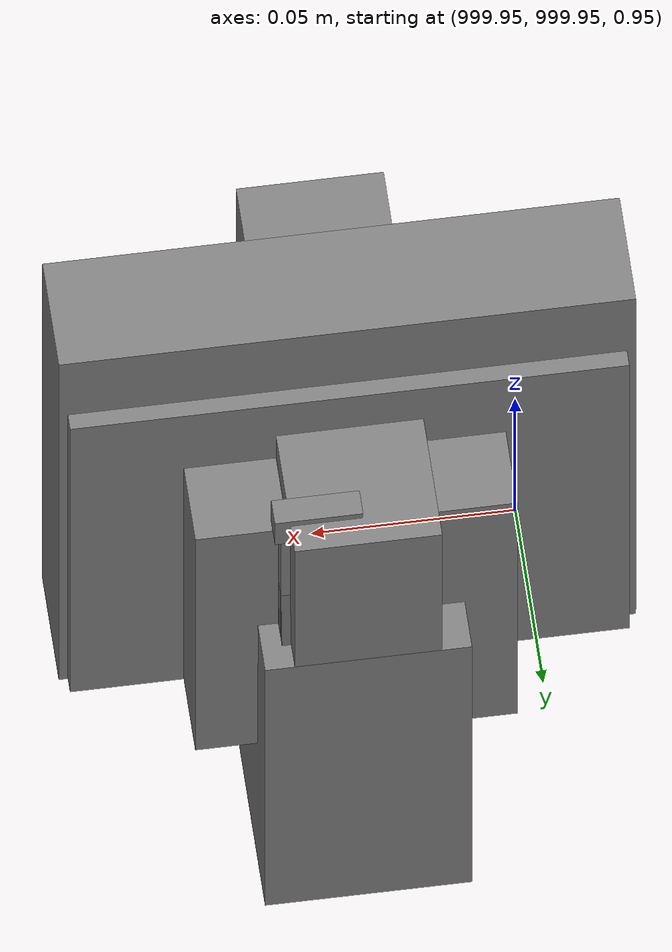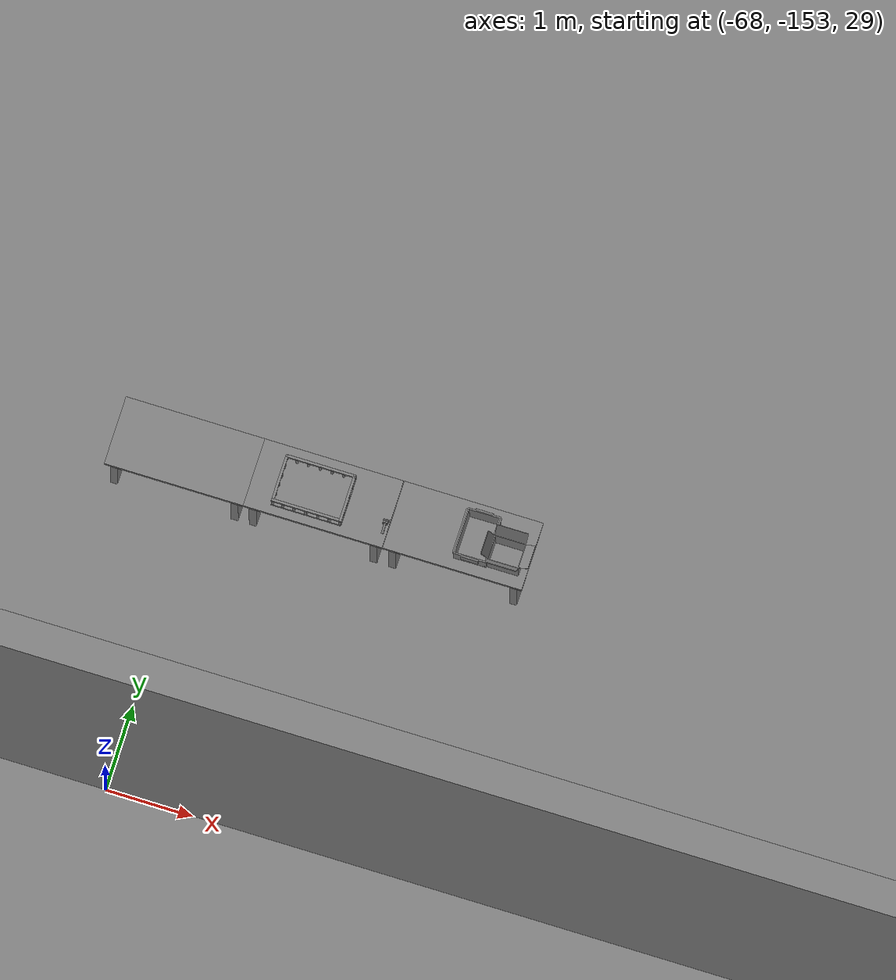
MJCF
<mujoco>
    <option gravity="0.000000000 0.000000000 -9.810000420" timestep="0.0049999999" integrator="implicitfast" density="1.225" viscosity="1.8000001e-05" noslip_iterations="10" iterations="100" sdf_iterations="50">
        <flag multiccd="disable"/>
    </option>
    <size memory="1000M"/>
    <compiler coordinate="local"/>
    <worldbody>
        <light cutoff="30" pos="0 1 1" dir="0 -1 -2"/>
        <light cutoff="30" pos="0 -1 1" dir="0 1 -2"/>
        <body pos="-65.900817871 -148.946670532 31.165405273" euler="-174.833312988 9.475221634 100.085021973" mocap="true" name="spotlight4_SpotLight"/>
        <body pos="1000.000000000 1000.000000000 1.000000000" euler="0.000000000 0.000000000 180.000000000" name="openloong_gripper_2f85_fix_base_usda_battery_01">
            <geom contype="1" conaffinity="1" density="1000" type="box" material="" rgba="0.500000000 0.500000000 0.500000000 1.000000000" solimp="0.899999976 0.949999988 0.001000000" friction="1.000000000 0.005000000 0.000100000" solref="0.020000000 1.000000000" margin="0" condim="3" group="0" pos="-0.011123657 -0.041940309 0.101691343" quat="1.000000000 0.000000000 0.000000000 0.000000000" size="0.010800000 0.003375000 0.004725000" name="openloong_gripper_2f85_fix_base_usda_geom_AEF27CCE_E55C_4EE3_8836_BA1E566B402D"/>
            <geom contype="1" conaffinity="1" density="1000" type="box" material="" rgba="0.500000000 0.500000000 0.500000000 1.000000000" solimp="0.899999976 0.949999988 0.001000000" friction="1.000000000 0.005000000 0.000100000" solref="0.020000000 1.000000000" margin="0" condim="3" group="0" pos="-0.010876465 -0.044247437 0.047066893" quat="0.998702705 -0.050920475 0.000000000 0.000000000" size="0.009450001 0.002700000 0.024975000" name="openloong_gripper_2f85_fix_base_usda_geom_EA62257D_09AA_4328_A112_D442AF52AD97"/>
            <geom contype="1" conaffinity="1" density="1000" type="box" material="" rgba="0.500000000 0.500000000 0.500000000 1.000000000" solimp="0.899999976 0.949999988 0.001000000" friction="1.000000000 0.005000000 0.000100000" solref="0.020000000 1.000000000" margin="0" condim="3" group="0" pos="-0.001235962 -0.000659180 0.047381196" quat="1.000000000 0.000000000 0.000000000 0.000000000" size="0.039420001 0.039150000 0.047250003" name="openloong_gripper_2f85_fix_base_usda_geom_CC834E85_B537_4105_B567_7506B48DFC6A"/>
            <geom contype="1" conaffinity="1" density="1000" type="box" material="" rgba="0.500000000 0.500000000 0.500000000 1.000000000" solimp="0.899999976 0.949999988 0.001000000" friction="1.000000000 0.005000000 0.000100000" solref="0.020000000 1.000000000" margin="0" condim="3" group="0" pos="-0.010876465 -0.039138794 0.009851727" quat="1.000000000 0.000000000 0.000000000 0.000000000" size="0.009450001 0.010800000 0.013500000" name="openloong_gripper_2f85_fix_base_usda_geom_7E93F8A0_B3D5_40FF_A60A_861316C35534"/>
            <geom contype="1" conaffinity="1" density="1000" type="box" material="" rgba="0.500000000 0.500000000 0.500000000 1.000000000" solimp="0.899999976 0.949999988 0.001000000" friction="1.000000000 0.005000000 0.000100000" solref="0.020000000 1.000000000" margin="0" condim="3" group="0" pos="-0.010876465 -0.041528322 0.071508206" quat="1.000000000 0.000000000 0.000000000 0.000000000" size="0.009450001 0.002700000 0.027000001" name="openloong_gripper_2f85_fix_base_usda_geom_8CC441FF_5506_4700_959B_A9384F9CDEA2"/>
            <freejoint name="openloong_gripper_2f85_fix_base_usda_battery_01_joint"/>
            <site size="0.005000000 0.005000000 0.005000000" rgba="0.500000000 0.500000000 0.500000000 1.000000000" pos="0.000000000 0.000000000 0.000000000" quat="0.999961913 0.008726500 0.000000000 0.000000000" group="0" type="sphere" name="openloong_gripper_2f85_fix_base_usda_battery_01site"/>
        </body>
        <body pos="1000.000000000 1000.000000000 1.000000000" euler="0.000000000 0.000000000 180.000000000" name="openloong_gripper_2f85_fix_base_usda_cpu_fan">
            <geom contype="1" conaffinity="1" density="1000" type="box" material="" rgba="0.500000000 0.500000000 0.500000000 1.000000000" solimp="0.899999976 0.949999988 0.001000000" friction="1.000000000 0.005000000 0.000100000" solref="0.020000000 1.000000000" margin="0" condim="3" group="0" pos="0.000000000 0.000000000 0.070034981" quat="0.000000000 0.000000000 0.000000000 1.000000000" size="0.070700005 0.014699999 0.070700005" name="openloong_gripper_2f85_fix_base_usda_geom_4569B410_3437_4150_800B_68B754EF2CE0"/>
            <freejoint name="openloong_gripper_2f85_fix_base_usda_cpu_fan_joint"/>
            <site size="0.005000000 0.005000000 0.005000000" rgba="0.500000000 0.500000000 0.500000000 1.000000000" pos="0.000000000 0.000000000 0.000000000" quat="0.999961913 0.008726535 0.000000000 0.000000000" group="0" type="sphere" name="openloong_gripper_2f85_fix_base_usda_cpu_fancsite"/>
        </body>
        <body pos="1000.000000000 1000.000000000 1.000000000" euler="0.000000000 0.000000000 180.000000000" name="openloong_gripper_2f85_fix_base_usda_wifi_box">
            <geom contype="1" conaffinity="1" density="1000" type="box" material="" rgba="0.500000000 0.500000000 0.500000000 1.000000000" solimp="0.899999976 0.949999988 0.001000000" friction="1.000000000 0.005000000 0.000100000" solref="0.020000000 1.000000000" margin="0" condim="3" group="0" pos="0.000000000 0.000000000 0.058978677" quat="0.000000000 0.000000047 0.000000000 1.000000000" size="0.068499997 0.018999999 0.059000000" name="openloong_gripper_2f85_fix_base_usda_geom_C5732551_BF42_43F1_906B_4A445662B43D"/>
            <freejoint name="openloong_gripper_2f85_fix_base_usda_wifi_box_joint"/>
            <site size="0.005000000 0.005000000 0.005000000" rgba="0.500000000 0.500000000 0.500000000 1.000000000" pos="0.000000000 0.000000000 0.000000000" quat="0.999961913 0.008726500 0.000000000 0.000000000" group="0" type="sphere" name="openloong_gripper_2f85_fix_base_usda_wifi_boxsite"/>
        </body>
        <body pos="1000.000000000 1000.000000000 1.000000000" euler="0.000011953 0.000005123 -179.999984741" name="openloong_gripper_2f85_fix_base_usda_intel_box">
            <geom contype="1" conaffinity="1" density="1000" type="box" material="" rgba="0.500000000 0.500000000 0.500000000 1.000000000" solimp="0.899999976 0.949999988 0.001000000" friction="1.000000000 0.005000000 0.000100000" solref="0.020000000 1.000000000" margin="0" condim="3" group="0" pos="0.000000000 -0.000067139 0.000082284" quat="0.707106709 0.000000225 0.000000253 0.707106650" size="0.052800003 0.025300000 0.052800003" name="openloong_gripper_2f85_fix_base_usda_geom_F45FDF6F_A665_438C_99FD_EFBF9B6CFFB7"/>
            <freejoint name="openloong_gripper_2f85_fix_base_usda_intel_box_joint"/>
            <site size="0.005000000 0.005000000 0.005000000" rgba="0.500000000 0.500000000 0.500000000 1.000000000" pos="0.000000000 0.000000000 0.000000000" quat="0.999961913 0.008726500 0.000000000 0.000000000" group="0" type="sphere" name="openloong_gripper_2f85_fix_base_usda_intel_boxsite"/>
        </body>
        <body pos="1000.000000000 999.999938965 1.000000000" euler="0.000000000 0.000000000 180.000000000" name="openloong_gripper_2f85_fix_base_usda_intelcore_i5">
            <geom contype="1" conaffinity="1" density="1000" type="box" material="" rgba="0.500000000 0.500000000 0.500000000 1.000000000" solimp="0.899999976 0.949999988 0.001000000" friction="1.000000000 0.005000000 0.000100000" solref="0.020000000 1.000000000" margin="0" condim="3" group="0" pos="0.000000000 0.000000000 0.051722717" quat="0.707106709 0.000000000 0.000000000 -0.707106769" size="0.052800000 0.018080002 0.052800000" name="openloong_gripper_2f85_fix_base_usda_geom_E2FD1115_A2CC_4656_9F47_9B2A86A6F11B"/>
            <freejoint name="openloong_gripper_2f85_fix_base_usda_intelcore_i5_joint"/>
            <site size="0.005000000 0.005000000 0.005000000" rgba="0.500000000 0.500000000 0.500000000 1.000000000" pos="0.000000000 0.000000000 0.000000000" quat="0.999961913 0.008726534 0.000000000 0.000000000" group="0" type="sphere" name="openloong_gripper_2f85_fix_base_usda_intelcore_i5site"/>
        </body>
        <body pos="-66.384788513 -149.618453979 31.163679123" euler="88.816078186 -72.593032837 77.403320312" mocap="true" name="spotlight1_SpotLight"/>
        <body pos="-65.939109802 -149.245620728 31.171247482" euler="177.726882935 -69.733566284 -27.716201782" mocap="true" name="spotlight2_SpotLight"/>
        <body pos="-64.866622925 -149.383972168 30.183746338" euler="89.999984741 89.999946594 0.000000000" name="openloong_gripper_2f85_fix_base_usda_bluebox_01">
            <geom contype="1" conaffinity="1" density="1000" type="box" material="" rgba="0.500000000 0.500000000 0.500000000 1.000000000" solimp="0.899999976 0.949999988 0.001000000" friction="1.000000000 0.005000000 0.000100000" solref="0.020000000 1.000000000" margin="0" condim="3" group="0" pos="0.276580811 0.187225342 0.000068665" quat="0.707106948 0.000077471 0.707106352 0.000077486" size="0.100000001 0.057999998 0.010000000" name="openloong_gripper_2f85_fix_base_usda_geom_605311E4_45A1_4730_BC00_F871963C9E95"/>
            <geom contype="1" conaffinity="1" density="1000" type="box" material="" rgba="0.500000000 0.500000000 0.500000000 1.000000000" solimp="0.899999976 0.949999988 0.001000000" friction="1.000000000 0.005000000 0.000100000" solref="0.020000000 1.000000000" margin="0" condim="3" group="0" pos="0.000000000 0.002883911 0.000000000" quat="0.999999881 0.000000000 0.000000000 0.000000000" size="0.254000008 0.003000000 0.172000006" name="openloong_gripper_2f85_fix_base_usda_geom_5FD5BCF3_CF74_4346_B907_B673C913A52D"/>
            <geom contype="1" conaffinity="1" density="1000" type="box" material="" rgba="0.500000000 0.500000000 0.500000000 1.000000000" solimp="0.899999976 0.949999988 0.001000000" friction="1.000000000 0.005000000 0.000100000" solref="0.020000000 1.000000000" margin="0" condim="3" group="0" pos="0.000000000 0.124874115 0.173484802" quat="0.999796331 0.020176515 -0.000000015 0.000000030" size="0.259999990 0.119999997 0.007000000" name="openloong_gripper_2f85_fix_base_usda_geom_4397516C_B844_4115_B6FD_D2C36457164B"/>
            <geom contype="1" conaffinity="1" density="1000" type="box" material="" rgba="0.500000000 0.500000000 0.500000000 1.000000000" solimp="0.899999976 0.949999988 0.001000000" friction="1.000000000 0.005000000 0.000100000" solref="0.020000000 1.000000000" margin="0" condim="3" group="0" pos="0.000000000 0.124874115 -0.173469543" quat="0.999796331 -0.020176545 -0.000000015 0.000000000" size="0.259999990 0.119999997 0.007000000" name="openloong_gripper_2f85_fix_base_usda_geom_FD689AB4_FEB4_47F1_9FA7_9985400BB0B8"/>
            <geom contype="1" conaffinity="1" density="1000" type="box" material="" rgba="0.500000000 0.500000000 0.500000000 1.000000000" solimp="0.899999976 0.949999988 0.001000000" friction="1.000000000 0.005000000 0.000100000" solref="0.020000000 1.000000000" margin="0" condim="3" group="0" pos="0.000000000 0.214008331 0.188980103" quat="0.999912977 0.013176724 0.000000015 0.000000000" size="0.259999990 0.029999999 0.012500000" name="openloong_gripper_2f85_fix_base_usda_geom_5AC719E9_0A88_42B9_A787_957BAB658C78"/>
            <geom contype="1" conaffinity="1" density="1000" type="box" material="" rgba="0.500000000 0.500000000 0.500000000 1.000000000" solimp="0.899999976 0.949999988 0.001000000" friction="1.000000000 0.005000000 0.000100000" solref="0.020000000 1.000000000" margin="0" condim="3" group="0" pos="-0.258361816 0.125289917 0.001876831" quat="0.702796936 -0.020792112 0.710783124 0.020769298" size="0.189999998 0.119999997 0.009000000" name="openloong_gripper_2f85_fix_base_usda_geom_5DCEA231_0AD9_426C_A0D1_8FFF7B210D53"/>
            <geom contype="1" conaffinity="1" density="1000" type="box" material="" rgba="0.500000000 0.500000000 0.500000000 1.000000000" solimp="0.899999976 0.949999988 0.001000000" friction="1.000000000 0.005000000 0.000100000" solref="0.020000000 1.000000000" margin="0" condim="3" group="0" pos="0.000000000 0.214008331 -0.188980103" quat="0.999912977 -0.013176769 0.000000030 0.000000015" size="0.259999990 0.029999999 0.012500000" name="openloong_gripper_2f85_fix_base_usda_geom_80DA64BE_7317_4AE8_A614_328564B47F1D"/>
            <geom contype="1" conaffinity="1" density="1000" type="box" material="" rgba="0.500000000 0.500000000 0.500000000 1.000000000" solimp="0.899999976 0.949999988 0.001000000" friction="1.000000000 0.005000000 0.000100000" solref="0.020000000 1.000000000" margin="0" condim="3" group="0" pos="-0.276611328 0.187225342 0.000068665" quat="0.707106650 0.000077441 0.707106709 0.000077456" size="0.100000001 0.057999998 0.010000000" name="openloong_gripper_2f85_fix_base_usda_geom_2DA1F951_0938_4EA5_BB74_8B9C40CE68E2"/>
            <geom contype="1" conaffinity="1" density="1000" type="box" material="" rgba="0.500000000 0.500000000 0.500000000 1.000000000" solimp="0.899999976 0.949999988 0.001000000" friction="1.000000000 0.005000000 0.000100000" solref="0.020000000 1.000000000" margin="0" condim="3" group="0" pos="0.258331299 0.125289917 0.001876831" quat="0.702851415 0.018856421 0.710823774 -0.019329369" size="0.189999998 0.119999997 0.009000000" name="openloong_gripper_2f85_fix_base_usda_geom_150B9437_743F_482C_BCED_526286079A7D"/>
            <freejoint name="openloong_gripper_2f85_fix_base_usda_bluebox_01_joint"/>
            <site size="0.005000000 0.005000000 0.005000000" rgba="0.500000000 0.500000000 0.500000000 1.000000000" pos="0.000000000 0.000000000 0.000000000" quat="0.999961913 0.008726534 0.000000000 0.000000000" group="0" type="sphere" name="openloong_gripper_2f85_fix_base_usda_bluebox_01site"/>
        </body>
        <body pos="-64.496299744 -149.491867065 30.235729218" euler="0.000000000 0.000000000 89.999946594" name="openloong_gripper_2f85_fix_base_usda_cardboardbox_01">
            <geom contype="1" conaffinity="1" density="1000" type="box" material="" rgba="0.500000000 0.500000000 0.500000000 1.000000000" solimp="0.899999976 0.949999988 0.001000000" friction="1.000000000 0.005000000 0.000100000" solref="0.020000000 1.000000000" margin="0" condim="3" group="0" pos="-0.003166199 -0.004086494 0.005052090" quat="1.000000000 0.000000000 0.000000000 0.000000000" size="0.142499998 0.177500010 0.005000000" name="openloong_gripper_2f85_fix_base_usda_geom_4119ECC9_19D5_4E9C_8349_BA4CE842B0BB"/>
            <geom contype="1" conaffinity="1" density="1000" type="box" material="" rgba="0.500000000 0.500000000 0.500000000 1.000000000" solimp="0.899999976 0.949999988 0.001000000" friction="1.000000000 0.005000000 0.000100000" solref="0.020000000 1.000000000" margin="0" condim="3" group="0" pos="-0.003166199 0.170316696 0.150570869" quat="1.000000000 0.000000000 0.000000000 0.000000000" size="0.142499998 0.005000000 0.149999991" name="openloong_gripper_2f85_fix_base_usda_geom_0FEB34A6_FE05_4651_AB42_8192F56181A6"/>
            <geom contype="1" conaffinity="1" density="1000" type="box" material="" rgba="0.500000000 0.500000000 0.500000000 1.000000000" solimp="0.899999976 0.949999988 0.001000000" friction="1.000000000 0.005000000 0.000100000" solref="0.020000000 1.000000000" margin="0" condim="3" group="0" pos="-0.147399902 -0.005307198 0.150570869" quat="1.000000000 0.000000000 0.000000000 0.000000000" size="0.005000000 0.177500010 0.149999991" name="openloong_gripper_2f85_fix_base_usda_geom_DADC817A_9C2E_4419_8AD2_1DE33534F822"/>
            <geom contype="1" conaffinity="1" density="1000" type="box" material="" rgba="0.500000000 0.500000000 0.500000000 1.000000000" solimp="0.899999976 0.949999988 0.001000000" friction="1.000000000 0.005000000 0.000100000" solref="0.020000000 1.000000000" margin="0" condim="3" group="0" pos="0.140275955 -0.005307198 0.150570869" quat="1.000000000 0.000000000 0.000000000 0.000000000" size="0.005000000 0.177500010 0.149999991" name="openloong_gripper_2f85_fix_base_usda_geom_0C066FB7_85E4_4594_A005_5141FC671A69"/>
            <geom contype="1" conaffinity="1" density="1000" type="box" material="" rgba="0.500000000 0.500000000 0.500000000 1.000000000" solimp="0.899999976 0.949999988 0.001000000" friction="1.000000000 0.005000000 0.000100000" solref="0.020000000 1.000000000" margin="0" condim="3" group="0" pos="-0.003166199 -0.181550980 0.150570869" quat="1.000000000 0.000000000 0.000000000 0.000000000" size="0.142499998 0.005000000 0.149999991" name="openloong_gripper_2f85_fix_base_usda_geom_D12933A6_08AE_4972_8AFA_7B2AD8B62CC4"/>
            <freejoint name="openloong_gripper_2f85_fix_base_usda_cardboardbox_01_joint"/>
            <site size="0.005000000 0.005000000 0.005000000" rgba="0.500000000 0.500000000 0.500000000 1.000000000" pos="0.000000000 0.000000000 0.000000000" quat="0.999961913 0.008726535 0.000000000 0.000000000" group="0" type="sphere" name="openloong_gripper_2f85_fix_base_usda_site_EDBE9C8E_00F6_42CE_82DA_2288C49985DC"/>
            <body pos="0.139160156 -0.004048347 0.301930904" euler="-179.999954224 49.383502960 179.999954224" name="openloong_gripper_2f85_fix_base_usda_A1_006">
                <geom contype="1" conaffinity="1" density="1000" type="box" material="" rgba="0.500000000 0.500000000 0.500000000 1.000000000" solimp="0.899999976 0.949999988 0.001000000" friction="1.000000000 0.005000000 0.000100000" solref="0.020000000 1.000000000" margin="0" condim="3" group="0" pos="-0.071587563 0.000009537 0.001745224" quat="0.999999881 0.000000000 0.000000000 0.000000000" size="0.071249999 0.179999992 0.002500000" name="openloong_gripper_2f85_fix_base_usda_geom_8373ABA2_E677_4879_945F_35B3E0F4FE57"/>
                <joint armature="0" stiffness="0.07" damping="0.0099999998" axis="0.000000 1.000000 0.000000" type="hinge" name="openloong_gripper_2f85_fix_base_usda_A1_006"/>
            </body>
            <body pos="-0.145902634 -0.004086494 0.301938057" euler="-180.000000000 -60.000011444 -180.000000000" name="openloong_gripper_2f85_fix_base_usda_A2_006">
                <geom contype="1" conaffinity="1" density="1000" type="box" material="" rgba="0.500000000 0.500000000 0.500000000 1.000000000" solimp="0.899999976 0.949999988 0.001000000" friction="1.000000000 0.005000000 0.000100000" solref="0.020000000 1.000000000" margin="0" condim="3" group="0" pos="0.071268082 0.000009537 0.002717972" quat="0.000002921 0.000000000 -0.000000030 0.999999881" size="0.071249999 0.179999992 0.002500000" name="openloong_gripper_2f85_fix_base_usda_geom_59FD6FB0_4123_41E9_B28B_FC33BE348567"/>
                <joint armature="0" stiffness="0.07" damping="0.0099999998" axis="0.000000 1.000000 0.000000" type="hinge" name="openloong_gripper_2f85_fix_base_usda_A2_006"/>
            </body>
            <body pos="-0.003385544 0.175991058 0.301930904" euler="-125.858116150 -0.000004561 0.000002331" name="openloong_gripper_2f85_fix_base_usda_B2_006">
                <geom contype="1" conaffinity="1" density="1000" type="box" material="" rgba="0.500000000 0.500000000 0.500000000 1.000000000" solimp="0.899999976 0.949999988 0.001000000" friction="1.000000000 0.005000000 0.000100000" solref="0.020000000 1.000000000" margin="0" condim="3" group="0" pos="0.000009537 -0.070939064 -0.002470016" quat="0.999614120 0.027776197 -0.000000015 0.000000030" size="0.137500003 0.064999998 0.005000000" name="openloong_gripper_2f85_fix_base_usda_geom_8A4E07D1_29BB_47F8_8C0F_18FD4D92CA2C"/>
                <joint armature="0" stiffness="0.07" damping="0.0099999998" axis="1.000000 0.000000 0.000000" type="hinge" name="openloong_gripper_2f85_fix_base_usda_B2_006"/>
            </body>
            <body pos="-0.003385544 -0.184140205 0.301938057" euler="147.805557251 0.000000000 0.000000000" name="openloong_gripper_2f85_fix_base_usda_B1_006">
                <geom contype="1" conaffinity="1" density="1000" type="box" material="" rgba="0.500000000 0.500000000 0.500000000 1.000000000" solimp="0.899999976 0.949999988 0.001000000" friction="1.000000000 0.005000000 0.000100000" solref="0.020000000 1.000000000" margin="0" condim="3" group="0" pos="-0.000028610 0.070202351 -0.002703667" quat="0.999614179 -0.027776167 0.000000000 0.000000000" size="0.137500003 0.064999998 0.005000000" name="openloong_gripper_2f85_fix_base_usda_geom_6018E0AE_F86D_4415_9446_43427C87AF5D"/>
                <joint armature="0" stiffness="0.07" damping="0.0099999998" axis="1.000000 0.000000 0.000000" type="hinge" name="openloong_gripper_2f85_fix_base_usda_B1_006"/>
            </body>
        </body>
        <body pos="-65.882858276 -149.481979370 30.229999542" euler="-64.487716675 0.000000000 0.000000000" name="openloong_gripper_2f85_fix_base_usda_Barcode">
            <geom contype="1" conaffinity="1" density="1000" type="box" material="" rgba="0.500000000 0.500000000 0.500000000 1.000000000" solimp="0.899999976 0.949999988 0.001000000" friction="1.000000000 0.005000000 0.000100000" solref="0.020000000 1.000000000" margin="0" condim="3" group="0" pos="0.000000000 0.013038635 0.001419067" quat="0.000000000 0.000000000 0.000000000 1.000000119" size="0.034000002 0.010000000 0.017999999" name="openloong_gripper_2f85_fix_base_usda_geom_050B5864_DB8E_49D4_96C6_E1A547F4D1EB"/>
            <geom contype="1" conaffinity="1" density="1000" type="box" material="" rgba="0.500000000 0.500000000 0.500000000 1.000000000" solimp="0.899999976 0.949999988 0.001000000" friction="1.000000000 0.005000000 0.000100000" solref="0.020000000 1.000000000" margin="0" condim="3" group="0" pos="0.000000000 -0.035301208 -0.007095337" quat="0.000000000 0.000000000 -0.043619365 0.999048233" size="0.028999999 0.010000000 0.020000000" name="openloong_gripper_2f85_fix_base_usda_geom_5BDD7DA4_5240_4BE7_8900_DC3D29AE2EA5"/>
            <geom contype="1" conaffinity="1" density="1000" type="box" material="" rgba="0.500000000 0.500000000 0.500000000 1.000000000" solimp="0.899999976 0.949999988 0.001000000" friction="1.000000000 0.005000000 0.000100000" solref="0.020000000 1.000000000" margin="0" condim="3" group="0" pos="0.000000000 -0.043411255 -0.011749268" quat="0.922262907 0.386563420 0.000000000 0.000000000" size="0.026000001 0.010000000 0.020000000" name="openloong_gripper_2f85_fix_base_usda_geom_F7A47BCA_6E2D_4CFD_84B1_092C5F8BEC7A"/>
            <geom contype="1" conaffinity="1" density="1000" type="box" material="" rgba="0.500000000 0.500000000 0.500000000 1.000000000" solimp="0.899999976 0.949999988 0.001000000" friction="1.000000000 0.005000000 0.000100000" solref="0.020000000 1.000000000" margin="0" condim="3" group="0" pos="0.000000000 -0.016967773 -0.031860352" quat="0.000000000 0.000000000 0.000000000 1.000000119" size="0.008000000 0.010000000 0.013000000" name="openloong_gripper_2f85_fix_base_usda_geom_ED8505F8_4214_47B3_8659_1B72C2409948"/>
            <geom contype="1" conaffinity="1" density="1000" type="box" material="" rgba="0.500000000 0.500000000 0.500000000 1.000000000" solimp="0.899999976 0.949999988 0.001000000" friction="1.000000000 0.005000000 0.000100000" solref="0.020000000 1.000000000" margin="0" condim="3" group="0" pos="0.000000000 -0.001869202 0.000312805" quat="0.953716993 0.300705761 0.000000000 0.000000000" size="0.032000002 0.010000000 0.018999999" name="openloong_gripper_2f85_fix_base_usda_geom_FE10DD65_6FBC_4E34_B61A_92226F70E543"/>
            <geom contype="1" conaffinity="1" density="1000" type="box" material="" rgba="0.500000000 0.500000000 0.500000000 1.000000000" solimp="0.899999976 0.949999988 0.001000000" friction="1.000000000 0.005000000 0.000100000" solref="0.020000000 1.000000000" margin="0" condim="3" group="0" pos="0.000000000 -0.019531250 -0.003173828" quat="0.953716993 0.300705761 0.000000000 0.000000000" size="0.030999999 0.010000000 0.020000000" name="openloong_gripper_2f85_fix_base_usda_geom_66FDD795_C938_4984_B217_73252130614F"/>
            <geom contype="1" conaffinity="1" density="1000" type="box" material="" rgba="0.500000000 0.500000000 0.500000000 1.000000000" solimp="0.899999976 0.949999988 0.001000000" friction="1.000000000 0.005000000 0.000100000" solref="0.020000000 1.000000000" margin="0" condim="3" group="0" pos="0.000000000 -0.035301208 -0.007095337" quat="0.953716993 0.300705761 0.000000000 0.000000000" size="0.028999999 0.010000000 0.020000000" name="openloong_gripper_2f85_fix_base_usda_geom_D9B67FA7_2709_44DD_92E4_E312A799969F"/>
            <geom contype="1" conaffinity="1" density="1000" type="box" material="" rgba="0.500000000 0.500000000 0.500000000 1.000000000" solimp="0.899999976 0.949999988 0.001000000" friction="1.000000000 0.005000000 0.000100000" solref="0.020000000 1.000000000" margin="0" condim="3" group="0" pos="0.000000000 -0.042617798 -0.071121216" quat="0.000000000 0.000000000 0.000000000 1.000000119" size="0.013000000 0.021000000 0.059999999" name="openloong_gripper_2f85_fix_base_usda_geom_F1AFD55E_4654_49F1_A1C8_AB22A489A45E"/>
            <freejoint name="openloong_gripper_2f85_fix_base_usda_Barcode_joint"/>
            <site size="0.005000000 0.005000000 0.005000000" rgba="0.500000000 0.500000000 0.500000000 1.000000000" pos="0.000000000 0.000000000 0.000000000" quat="1.000000000 0.000000000 0.000000000 0.000000000" group="0" type="sphere" name="openloong_gripper_2f85_fix_base_usda_Barcode_site"/>
        </body>
        <body pos="-66.745018005 -149.392349243 30.184000015" euler="0.000000000 0.000000000 89.999946594" name="[22332807422047]_Basket_01">
            <geom contype="1" conaffinity="1" density="1000" type="box" material="" rgba="0.500000000 0.500000000 0.500000000 1.000000000" solimp="0.899999976 0.949999988 0.001000000" friction="1.000000000 0.005000000 0.000100000" solref="0.020000000 1.000000000" margin="0" condim="3" group="0" pos="-0.052425385 0.389207840 0.089787483" quat="0.707107008 0.000000000 0.000000000 0.707106411" size="0.014249999 0.014249999 0.059999999" name="[22332807422047]_geom_B5AAA292_E9A2_4CA8_AEBC_BF2FC67FB8C2"/>
            <geom contype="1" conaffinity="1" density="1000" type="box" material="" rgba="0.500000000 0.500000000 0.500000000 1.000000000" solimp="0.899999976 0.949999988 0.001000000" friction="1.000000000 0.005000000 0.000100000" solref="0.020000000 1.000000000" margin="0" condim="3" group="0" pos="0.264015198 -0.133043289 0.089787483" quat="0.707107008 0.000000000 0.000000000 0.707106411" size="0.014249999 0.014249999 0.059999999" name="[22332807422047]_geom_43660083_FC00_4604_A66C_0CAB8A1CF0CB"/>
            <geom contype="1" conaffinity="1" density="1000" type="box" material="" rgba="0.500000000 0.500000000 0.500000000 1.000000000" solimp="0.899999976 0.949999988 0.001000000" friction="1.000000000 0.005000000 0.000100000" solref="0.020000000 1.000000000" margin="0" condim="3" group="0" pos="-0.264015198 -0.265548706 0.089793205" quat="0.707107008 0.000000000 0.000000000 0.707106411" size="0.014249999 0.014249999 0.059999999" name="[22332807422047]_geom_65A02544_274A_4FC9_B235_F972A82B584A"/>
            <geom contype="1" conaffinity="1" density="1000" type="box" material="" rgba="0.500000000 0.500000000 0.500000000 1.000000000" solimp="0.899999976 0.949999988 0.001000000" friction="1.000000000 0.005000000 0.000100000" solref="0.020000000 1.000000000" margin="0" condim="3" group="0" pos="-0.160263062 -0.389322281 0.089793205" quat="0.707107008 0.000000000 0.000000000 0.707106411" size="0.014249999 0.014249999 0.059999999" name="[22332807422047]_geom_9FF96846_8743_462C_B9B1_4F99ED0C3966"/>
            <geom contype="1" conaffinity="1" density="1000" type="box" material="" rgba="0.500000000 0.500000000 0.500000000 1.000000000" solimp="0.899999976 0.949999988 0.001000000" friction="1.000000000 0.005000000 0.000100000" solref="0.020000000 1.000000000" margin="0" condim="3" group="0" pos="0.162265778 -0.389322281 0.089787483" quat="0.707107008 0.000000000 0.000000000 0.707106411" size="0.014249999 0.014249999 0.059999999" name="[22332807422047]_geom_41D6879F_6954_420D_81A3_4B5AC47F8928"/>
            <geom contype="1" conaffinity="1" density="1000" type="box" material="" rgba="0.500000000 0.500000000 0.500000000 1.000000000" solimp="0.899999976 0.949999988 0.001000000" friction="1.000000000 0.005000000 0.000100000" solref="0.020000000 1.000000000" margin="0" condim="3" group="0" pos="0.264015198 0.389207840 0.089787483" quat="0.707107008 0.000000000 0.000000000 0.707106411" size="0.014249999 0.014249999 0.059999999" name="[22332807422047]_geom_098E9C8E_99E3_4C83_A858_429F14513902"/>
            <geom contype="1" conaffinity="1" density="1000" type="box" material="" rgba="0.500000000 0.500000000 0.500000000 1.000000000" solimp="0.899999976 0.949999988 0.001000000" friction="1.000000000 0.005000000 0.000100000" solref="0.020000000 1.000000000" margin="0" condim="3" group="0" pos="-0.264015198 -0.133043289 0.089793205" quat="0.707107008 0.000000000 0.000000000 0.707106411" size="0.014249999 0.014249999 0.059999999" name="[22332807422047]_geom_822D320F_6F89_47AC_870C_2F2EE19294A8"/>
            <geom contype="1" conaffinity="1" density="1000" type="box" material="" rgba="0.500000000 0.500000000 0.500000000 1.000000000" solimp="0.899999976 0.949999988 0.001000000" friction="1.000000000 0.005000000 0.000100000" solref="0.020000000 1.000000000" margin="0" condim="3" group="0" pos="-0.264026642 0.269256592 0.089793205" quat="0.707107008 0.000000000 0.000000000 0.707106411" size="0.014249999 0.014249999 0.059999999" name="[22332807422047]_geom_C6FC422B_8D64_42DF_BB04_0059C3C5FFB2"/>
            <geom contype="1" conaffinity="1" density="1000" type="box" material="" rgba="0.500000000 0.500000000 0.500000000 1.000000000" solimp="0.899999976 0.949999988 0.001000000" friction="1.000000000 0.005000000 0.000100000" solref="0.020000000 1.000000000" margin="0" condim="3" group="0" pos="0.054462433 0.389207840 0.089787483" quat="0.707107008 0.000000000 0.000000000 0.707106411" size="0.014249999 0.014249999 0.059999999" name="[22332807422047]_geom_763FDA1F_A04A_468A_AB88_0A9A5016BE3C"/>
            <geom contype="1" conaffinity="1" density="1000" type="box" material="" rgba="0.500000000 0.500000000 0.500000000 1.000000000" solimp="0.899999976 0.949999988 0.001000000" friction="1.000000000 0.005000000 0.000100000" solref="0.020000000 1.000000000" margin="0" condim="3" group="0" pos="0.054462433 -0.389322281 0.089787483" quat="0.707107008 0.000000000 0.000000000 0.707106411" size="0.014249999 0.014249999 0.059999999" name="[22332807422047]_geom_F5DE289D_ED7A_49A3_B342_AFC5793E396B"/>
            <geom contype="1" conaffinity="1" density="1000" type="box" material="" rgba="0.500000000 0.500000000 0.500000000 1.000000000" solimp="0.899999976 0.949999988 0.001000000" friction="1.000000000 0.005000000 0.000100000" solref="0.020000000 1.000000000" margin="0" condim="3" group="0" pos="0.264015198 0.269256592 0.089793205" quat="0.707107008 0.000000000 0.000000000 0.707106411" size="0.014249999 0.014249999 0.059999999" name="[22332807422047]_geom_EC5B36A4_DCCC_4AE5_A810_20FF8D7F4868"/>
            <geom contype="1" conaffinity="1" density="1000" type="box" material="" rgba="0.500000000 0.500000000 0.500000000 1.000000000" solimp="0.899999976 0.949999988 0.001000000" friction="1.000000000 0.005000000 0.000100000" solref="0.020000000 1.000000000" margin="0" condim="3" group="0" pos="0.264015198 -0.389322281 0.089787483" quat="0.707107008 0.000000000 0.000000000 0.707106411" size="0.014249999 0.014249999 0.059999999" name="[22332807422047]_geom_17F655A8_7493_4481_B2A9_B1442C10F02E"/>
            <geom contype="1" conaffinity="1" density="1000" type="box" material="" rgba="0.500000000 0.500000000 0.500000000 1.000000000" solimp="0.899999976 0.949999988 0.001000000" friction="1.000000000 0.005000000 0.000100000" solref="0.020000000 1.000000000" margin="0" condim="3" group="0" pos="0.000000000 0.000000000 0.015998840" quat="0.707107008 0.000000000 0.000000000 0.707106411" size="0.403499991 0.279000014 0.015750000" name="[22332807422047]_geom_3B35C189_07C1_4973_BDFA_2035700D0640"/>
            <geom contype="1" conaffinity="1" density="1000" type="box" material="" rgba="0.500000000 0.500000000 0.500000000 1.000000000" solimp="0.899999976 0.949999988 0.001000000" friction="1.000000000 0.005000000 0.000100000" solref="0.020000000 1.000000000" margin="0" condim="3" group="0" pos="0.000000000 -0.389476776 0.163619041" quat="0.707107008 0.000000000 0.000000000 0.707106411" size="0.015000000 0.277500004 0.015750000" name="[22332807422047]_geom_D01E00A3_A8F8_4B3E_A534_4677D54C394E"/>
            <geom contype="1" conaffinity="1" density="1000" type="box" material="" rgba="0.500000000 0.500000000 0.500000000 1.000000000" solimp="0.899999976 0.949999988 0.001000000" friction="1.000000000 0.005000000 0.000100000" solref="0.020000000 1.000000000" margin="0" condim="3" group="0" pos="0.162265778 0.389207840 0.089787483" quat="0.707107008 0.000000000 0.000000000 0.707106411" size="0.014249999 0.014249999 0.059999999" name="[22332807422047]_geom_780E64D7_90E1_4FD3_9D79_4324445EF360"/>
            <geom contype="1" conaffinity="1" density="1000" type="box" material="" rgba="0.500000000 0.500000000 0.500000000 1.000000000" solimp="0.899999976 0.949999988 0.001000000" friction="1.000000000 0.005000000 0.000100000" solref="0.020000000 1.000000000" margin="0" condim="3" group="0" pos="0.000000000 0.389471054 0.163619041" quat="0.707107008 0.000000000 0.000000000 0.707106411" size="0.015000000 0.277500004 0.015750000" name="[22332807422047]_geom_88CEE9FB_0685_4140_A5D9_FDFA908AB22D"/>
            <geom contype="1" conaffinity="1" density="1000" type="box" material="" rgba="0.500000000 0.500000000 0.500000000 1.000000000" solimp="0.899999976 0.949999988 0.001000000" friction="1.000000000 0.005000000 0.000100000" solref="0.020000000 1.000000000" margin="0" condim="3" group="0" pos="-0.263511658 0.000000000 0.163619041" quat="0.707107008 0.000000000 0.000000000 0.707106411" size="0.403499991 0.015000000 0.015750000" name="[22332807422047]_geom_BD7A17F4_559E_4691_86D3_E1A816315887"/>
            <geom contype="1" conaffinity="1" density="1000" type="box" material="" rgba="0.500000000 0.500000000 0.500000000 1.000000000" solimp="0.899999976 0.949999988 0.001000000" friction="1.000000000 0.005000000 0.000100000" solref="0.020000000 1.000000000" margin="0" condim="3" group="0" pos="-0.264015198 0.141334534 0.089793205" quat="0.707107008 0.000000000 0.000000000 0.707106411" size="0.014249999 0.014249999 0.059999999" name="[22332807422047]_geom_B73B2D2D_AEF3_4FC2_942F_276CF30004F2"/>
            <geom contype="1" conaffinity="1" density="1000" type="box" material="" rgba="0.500000000 0.500000000 0.500000000 1.000000000" solimp="0.899999976 0.949999988 0.001000000" friction="1.000000000 0.005000000 0.000100000" solref="0.020000000 1.000000000" margin="0" condim="3" group="0" pos="0.264015198 -0.265548706 0.089787483" quat="0.707107008 0.000000000 0.000000000 0.707106411" size="0.014249999 0.014249999 0.059999999" name="[22332807422047]_geom_B0FE6D40_F966_4668_883A_15DF9367C5C9"/>
            <geom contype="1" conaffinity="1" density="1000" type="box" material="" rgba="0.500000000 0.500000000 0.500000000 1.000000000" solimp="0.899999976 0.949999988 0.001000000" friction="1.000000000 0.005000000 0.000100000" solref="0.020000000 1.000000000" margin="0" condim="3" group="0" pos="-0.160263062 0.389207840 0.089787483" quat="0.707107008 0.000000000 0.000000000 0.707106411" size="0.014249999 0.014249999 0.059999999" name="[22332807422047]_geom_928EA35D_B1F0_44E2_ABA7_045DEA2CE475"/>
            <geom contype="1" conaffinity="1" density="1000" type="box" material="" rgba="0.500000000 0.500000000 0.500000000 1.000000000" solimp="0.899999976 0.949999988 0.001000000" friction="1.000000000 0.005000000 0.000100000" solref="0.020000000 1.000000000" margin="0" condim="3" group="0" pos="-0.052425385 -0.389322281 0.089787483" quat="0.707107008 0.000000000 0.000000000 0.707106411" size="0.014249999 0.014249999 0.059999999" name="[22332807422047]_geom_DD153DDA_14B2_4ED9_9D20_155C71AD0DB7"/>
            <geom contype="1" conaffinity="1" density="1000" type="box" material="" rgba="0.500000000 0.500000000 0.500000000 1.000000000" solimp="0.899999976 0.949999988 0.001000000" friction="1.000000000 0.005000000 0.000100000" solref="0.020000000 1.000000000" margin="0" condim="3" group="0" pos="-0.264026642 -0.389322281 0.089793205" quat="0.707107008 0.000000000 0.000000000 0.707106411" size="0.014249999 0.014249999 0.059999999" name="[22332807422047]_geom_8739EF17_5592_46E0_9093_BCB5111EA655"/>
            <geom contype="1" conaffinity="1" density="1000" type="box" material="" rgba="0.500000000 0.500000000 0.500000000 1.000000000" solimp="0.899999976 0.949999988 0.001000000" friction="1.000000000 0.005000000 0.000100000" solref="0.020000000 1.000000000" margin="0" condim="3" group="0" pos="0.264015198 0.141334534 0.089787483" quat="0.707107008 0.000000000 0.000000000 0.707106411" size="0.014249999 0.014249999 0.059999999" name="[22332807422047]_geom_0380BBDE_42AC_4B29_B140_17E55F3DB324"/>
            <geom contype="1" conaffinity="1" density="1000" type="box" material="" rgba="0.500000000 0.500000000 0.500000000 1.000000000" solimp="0.899999976 0.949999988 0.001000000" friction="1.000000000 0.005000000 0.000100000" solref="0.020000000 1.000000000" margin="0" condim="3" group="0" pos="-0.264015198 0.389207840 0.089793205" quat="0.707107008 0.000000000 0.000000000 0.707106411" size="0.014249999 0.014249999 0.059999999" name="[22332807422047]_geom_1B41389A_2C8D_45E6_AA9D_1B01941B2416"/>
            <geom contype="1" conaffinity="1" density="1000" type="box" material="" rgba="0.500000000 0.500000000 0.500000000 1.000000000" solimp="0.899999976 0.949999988 0.001000000" friction="1.000000000 0.005000000 0.000100000" solref="0.020000000 1.000000000" margin="0" condim="3" group="0" pos="0.264015198 0.004480362 0.089787483" quat="0.707107008 0.000000000 0.000000000 0.707106411" size="0.014249999 0.014249999 0.059999999" name="[22332807422047]_geom_EAEF23F7_83C4_4B59_8A9C_79CCB8CD36D7"/>
            <geom contype="1" conaffinity="1" density="1000" type="box" material="" rgba="0.500000000 0.500000000 0.500000000 1.000000000" solimp="0.899999976 0.949999988 0.001000000" friction="1.000000000 0.005000000 0.000100000" solref="0.020000000 1.000000000" margin="0" condim="3" group="0" pos="0.263694763 -0.000011444 0.163619041" quat="0.707107008 0.000000000 0.000000000 0.707106411" size="0.403499991 0.015000000 0.015750000" name="[22332807422047]_geom_3432A1EA_89DA_45D4_A598_84C9D8DD0DC2"/>
            <geom contype="1" conaffinity="1" density="1000" type="box" material="" rgba="0.500000000 0.500000000 0.500000000 1.000000000" solimp="0.899999976 0.949999988 0.001000000" friction="1.000000000 0.005000000 0.000100000" solref="0.020000000 1.000000000" margin="0" condim="3" group="0" pos="-0.264015198 0.004480362 0.089793205" quat="0.707107008 0.000000000 0.000000000 0.707106411" size="0.014249999 0.014249999 0.059999999" name="[22332807422047]_geom_4220946F_6866_450D_AEAA_B8502B645CFC"/>
            <freejoint name="[22332807422047]_joint_85B13728_21DB_4538_B0B5_1C9C77076B40"/>
        </body>
        <body pos="0.000000000 0.000000000 0.000000000" euler="0.000000000 0.000000000 0.000000000" name="Static Objects_Static Objects">
            <geom contype="1" conaffinity="1" density="1000" type="box" material="" rgba="0.500000000 0.500000000 0.500000000 1.000000000" solimp="0.899999976 0.949999988 0.001000000" friction="1.000000000 0.005000000 0.000100000" solref="0.020000000 1.000000000" margin="0" condim="3" group="0" pos="-67.544113159 -149.365814209 29.727830887" quat="0.500000417 0.499999970 0.499999553 0.499999970" size="0.381000012 0.319999993 0.041000001" name="Static Objects_geom_C8D5AF85_8C1D_48A2_8274_F6D6F1C6D11F"/>
            <geom contype="1" conaffinity="1" density="1000" type="box" material="" rgba="0.500000000 0.500000000 0.500000000 1.000000000" solimp="0.899999976 0.949999988 0.001000000" friction="1.000000000 0.005000000 0.000100000" solref="0.020000000 1.000000000" margin="0" condim="3" group="0" pos="-68.239501953 -149.365814209 30.086868286" quat="0.500000417 0.499999970 0.499999553 0.499999970" size="0.370999992 0.039500002 0.745000005" name="Static Objects_geom_9D94D1F3_6A8D_4B67_BB04_400718F6CF71"/>
            <geom contype="1" conaffinity="1" density="1000" type="box" material="" rgba="0.500000000 0.500000000 0.500000000 1.000000000" solimp="0.899999976 0.949999988 0.001000000" friction="1.000000000 0.005000000 0.000100000" solref="0.020000000 1.000000000" margin="0" condim="3" group="0" pos="-68.239501953 -149.365814209 30.147235870" quat="0.500000417 0.499999970 0.499999553 0.499999970" size="0.400000006 0.022000000 0.800000012" name="Static Objects_geom_B8DFA626_EEC6_4DF5_B52E_02C4A0D3020F"/>
            <geom contype="1" conaffinity="1" density="1000" type="box" material="" rgba="0.500000000 0.500000000 0.500000000 1.000000000" solimp="0.899999976 0.949999988 0.001000000" friction="1.000000000 0.005000000 0.000100000" solref="0.020000000 1.000000000" margin="0" condim="3" group="0" pos="-68.934890747 -149.365814209 29.727830887" quat="0.500000417 0.499999970 0.499999553 0.499999970" size="0.381000012 0.319999993 0.041000001" name="Static Objects_geom_898FB45E_9D50_4195_BDE6_83D7BBE695BF"/>
            <geom contype="1" conaffinity="1" density="1000" type="box" material="" rgba="0.500000000 0.500000000 0.500000000 1.000000000" solimp="0.899999976 0.949999988 0.001000000" friction="1.000000000 0.005000000 0.000100000" solref="0.020000000 1.000000000" margin="0" condim="3" group="0" pos="-68.239501953 -149.365814209 29.561563492" quat="0.500000417 0.499999970 0.499999553 0.499999970" size="0.020000000 0.022000000 0.660000026" name="Static Objects_geom_F96E4CE8_1DAF_4F86_8D11_A05E53E89FC4"/>
            <geom contype="1" conaffinity="1" density="1000" type="box" material="" rgba="0.500000000 0.500000000 0.500000000 1.000000000" solimp="0.899999976 0.949999988 0.001000000" friction="1.000000000 0.005000000 0.000100000" solref="0.020000000 1.000000000" margin="0" condim="3" group="0" pos="-65.945671082 -149.365814209 29.727830887" quat="0.500000417 0.499999970 0.499999553 0.499999970" size="0.381000012 0.319999993 0.041000001" name="Static Objects_geom_6FB334ED_A47B_45A8_BCA9_1D7D4C633ABD"/>
            <geom contype="1" conaffinity="1" density="1000" type="box" material="" rgba="0.500000000 0.500000000 0.500000000 1.000000000" solimp="0.899999976 0.949999988 0.001000000" friction="1.000000000 0.005000000 0.000100000" solref="0.020000000 1.000000000" margin="0" condim="3" group="0" pos="-66.641059875 -149.365814209 30.086868286" quat="0.500000417 0.499999970 0.499999553 0.499999970" size="0.370999992 0.039500002 0.745000005" name="Static Objects_geom_6C8E6289_1895_454D_88B0_39D2C7669EF9"/>
            <geom contype="1" conaffinity="1" density="1000" type="box" material="" rgba="0.500000000 0.500000000 0.500000000 1.000000000" solimp="0.899999976 0.949999988 0.001000000" friction="1.000000000 0.005000000 0.000100000" solref="0.020000000 1.000000000" margin="0" condim="3" group="0" pos="-66.641059875 -149.365814209 30.147235870" quat="0.500000417 0.499999970 0.499999553 0.499999970" size="0.400000006 0.022000000 0.800000012" name="Static Objects_geom_39515CF9_5075_438C_8B19_EB47C228BBF5"/>
            <geom contype="1" conaffinity="1" density="1000" type="box" material="" rgba="0.500000000 0.500000000 0.500000000 1.000000000" solimp="0.899999976 0.949999988 0.001000000" friction="1.000000000 0.005000000 0.000100000" solref="0.020000000 1.000000000" margin="0" condim="3" group="0" pos="-67.336448669 -149.365814209 29.727830887" quat="0.500000417 0.499999970 0.499999553 0.499999970" size="0.381000012 0.319999993 0.041000001" name="Static Objects_geom_F8287358_8EA2_407F_A34D_1E867EAB1DED"/>
            <geom contype="1" conaffinity="1" density="1000" type="box" material="" rgba="0.500000000 0.500000000 0.500000000 1.000000000" solimp="0.899999976 0.949999988 0.001000000" friction="1.000000000 0.005000000 0.000100000" solref="0.020000000 1.000000000" margin="0" condim="3" group="0" pos="-66.641059875 -149.365814209 29.561563492" quat="0.500000417 0.499999970 0.499999553 0.499999970" size="0.020000000 0.022000000 0.660000026" name="Static Objects_geom_AEEC7056_B9AF_427E_9F75_EEB8B286738B"/>
            <geom contype="1" conaffinity="1" density="1000" type="box" material="" rgba="0.500000000 0.500000000 0.500000000 1.000000000" solimp="0.899999976 0.949999988 0.001000000" friction="1.000000000 0.005000000 0.000100000" solref="0.020000000 1.000000000" margin="0" condim="3" group="0" pos="-64.338577271 -149.365814209 29.727830887" quat="0.500000417 0.499999970 0.499999553 0.499999970" size="0.381000012 0.319999993 0.041000001" name="Static Objects_geom_14948C85_0CC5_47D6_8F85_185B6BF4CB8E"/>
            <geom contype="1" conaffinity="1" density="1000" type="box" material="" rgba="0.500000000 0.500000000 0.500000000 1.000000000" solimp="0.899999976 0.949999988 0.001000000" friction="1.000000000 0.005000000 0.000100000" solref="0.020000000 1.000000000" margin="0" condim="3" group="0" pos="-65.033966064 -149.365814209 30.086868286" quat="0.500000417 0.499999970 0.499999553 0.499999970" size="0.370999992 0.039500002 0.745000005" name="Static Objects_geom_46301C2F_C898_409B_9A35_3CFA8A90762A"/>
            <geom contype="1" conaffinity="1" density="1000" type="box" material="" rgba="0.500000000 0.500000000 0.500000000 1.000000000" solimp="0.899999976 0.949999988 0.001000000" friction="1.000000000 0.005000000 0.000100000" solref="0.020000000 1.000000000" margin="0" condim="3" group="0" pos="-65.033966064 -149.365814209 30.147235870" quat="0.500000417 0.499999970 0.499999553 0.499999970" size="0.400000006 0.022000000 0.800000012" name="Static Objects_geom_7B70911A_F716_4E47_94DC_F7A5EEBCB874"/>
            <geom contype="1" conaffinity="1" density="1000" type="box" material="" rgba="0.500000000 0.500000000 0.500000000 1.000000000" solimp="0.899999976 0.949999988 0.001000000" friction="1.000000000 0.005000000 0.000100000" solref="0.020000000 1.000000000" margin="0" condim="3" group="0" pos="-65.729354858 -149.365814209 29.727830887" quat="0.500000417 0.499999970 0.499999553 0.499999970" size="0.381000012 0.319999993 0.041000001" name="Static Objects_geom_CD180274_1983_46B7_AF45_3FE75ED22E75"/>
            <geom contype="1" conaffinity="1" density="1000" type="box" material="" rgba="0.500000000 0.500000000 0.500000000 1.000000000" solimp="0.899999976 0.949999988 0.001000000" friction="1.000000000 0.005000000 0.000100000" solref="0.020000000 1.000000000" margin="0" condim="3" group="0" pos="-65.033966064 -149.365814209 29.561563492" quat="0.500000417 0.499999970 0.499999553 0.499999970" size="0.020000000 0.022000000 0.660000026" name="Static Objects_geom_EE76BFDC_08DC_4C20_BE2D_0C39B2067AA5"/>
            <geom contype="1" conaffinity="1" density="1000" type="box" material="" rgba="0.500000000 0.500000000 0.500000000 1.000000000" solimp="0.899999976 0.949999988 0.001000000" friction="1.000000000 0.005000000 0.000100000" solref="0.020000000 1.000000000" margin="0" condim="3" group="0" pos="-61.754566193 -137.853729248 33.906845093" quat="0.707107067 0.000000000 0.000000000 0.707106471" size="0.759999990 0.759999990 4.500000000" name="Static Objects_geom_605FF149_F27D_4A5C_8ECD_6CA831D315AE"/>
            <geom contype="1" conaffinity="1" density="1000" type="box" material="" rgba="0.500000000 0.500000000 0.500000000 1.000000000" solimp="0.899999976 0.949999988 0.001000000" friction="1.000000000 0.005000000 0.000100000" solref="0.020000000 1.000000000" margin="0" condim="3" group="0" pos="-57.511135101 -144.927108765 31.707921982" quat="1.000000000 0.000000000 0.000000000 0.000000000" size="0.200000003 8.000000000 2.299999952" name="Static Objects_geom_915FE8C7_F34B_4D8B_B405_D10105327FC8"/>
            <geom contype="1" conaffinity="1" density="1000" type="box" material="" rgba="0.500000000 0.500000000 0.500000000 1.000000000" solimp="0.899999976 0.949999988 0.001000000" friction="1.000000000 0.005000000 0.000100000" solref="0.020000000 1.000000000" margin="0" condim="3" group="0" pos="-80.517646790 -157.574050903 31.688196182" quat="0.707107067 0.000000000 0.000000000 0.707106471" size="0.600000024 0.600000024 2.299999952" name="Static Objects_geom_2AB8E99C_EFD0_4E38_9C60_B9720E9D77B7"/>
            <geom contype="1" conaffinity="1" density="1000" type="box" material="" rgba="0.500000000 0.500000000 0.500000000 1.000000000" solimp="0.899999976 0.949999988 0.001000000" friction="1.000000000 0.005000000 0.000100000" solref="0.020000000 1.000000000" margin="0" condim="3" group="0" pos="-80.711044312 -147.414932251 31.666158676" quat="1.000000000 0.000000000 0.000000000 0.000000000" size="0.200000003 10.000000000 2.299999952" name="Static Objects_geom_C062382C_D6D4_4A73_86BC_1E8C82CA400C"/>
            <geom contype="1" conaffinity="1" density="1000" type="box" material="" rgba="0.500000000 0.500000000 0.500000000 1.000000000" solimp="0.899999976 0.949999988 0.001000000" friction="1.000000000 0.005000000 0.000100000" solref="0.020000000 1.000000000" margin="0" condim="3" group="0" pos="-57.687217712 -137.434692383 31.688196182" quat="0.707107067 0.000000000 0.000000000 0.707106471" size="0.600000024 0.600000024 2.299999952" name="Static Objects_geom_FCC371F0_53B8_4110_99FA_9D7560745CD8"/>
            <geom contype="1" conaffinity="1" density="1000" type="box" material="" rgba="0.500000000 0.500000000 0.500000000 1.000000000" solimp="0.899999976 0.949999988 0.001000000" friction="1.000000000 0.005000000 0.000100000" solref="0.020000000 1.000000000" margin="0" condim="3" group="0" pos="-69.537033081 -140.263229370 31.714921951" quat="0.707107067 0.000000000 0.000000000 0.707106471" size="0.759999990 4.500000000 2.299999952" name="Static Objects_geom_79EED650_154E_4C37_BDDA_8F4D37961B56"/>
            <geom contype="1" conaffinity="1" density="1000" type="box" material="" rgba="0.500000000 0.500000000 0.500000000 1.000000000" solimp="0.899999976 0.949999988 0.001000000" friction="1.000000000 0.005000000 0.000100000" solref="0.020000000 1.000000000" margin="0" condim="3" group="0" pos="-80.073638916 -137.853713989 33.906845093" quat="0.707107067 0.000000000 0.000000000 0.707106471" size="0.759999990 0.759999990 4.500000000" name="Static Objects_geom_CFACAF1E_E6D9_4D13_A231_9241A58073E7"/>
            <geom contype="1" conaffinity="1" density="1000" type="box" material="" rgba="0.500000000 0.500000000 0.500000000 1.000000000" solimp="0.899999976 0.949999988 0.001000000" friction="1.000000000 0.005000000 0.000100000" solref="0.020000000 1.000000000" margin="0" condim="3" group="0" pos="-73.406707764 -155.734664917 31.707921982" quat="1.000000000 0.000000000 0.000000000 0.000000000" size="0.200000003 3.000000000 2.299999952" name="Static Objects_geom_2792DC71_5EBC_44FC_BCD8_96AF7F0CE779"/>
            <geom contype="1" conaffinity="1" density="1000" type="box" material="" rgba="0.500000000 0.500000000 0.500000000 1.000000000" solimp="0.899999976 0.949999988 0.001000000" friction="1.000000000 0.005000000 0.000100000" solref="0.020000000 1.000000000" margin="0" condim="3" group="0" pos="-68.497543335 -137.448257446 31.707921982" quat="0.707107067 0.000000000 0.000000000 0.707106471" size="0.200000003 14.000000000 2.299999952" name="Static Objects_geom_A8D41C04_1C3C_4AF1_AE28_81B6F083E655"/>
            <geom contype="1" conaffinity="1" density="1000" type="cylinder" material="" rgba="0.500000000 0.500000000 0.500000000 1.000000000" solimp="0.899999976 0.949999988 0.001000000" friction="1.000000000 0.005000000 0.000100000" solref="0.020000000 1.000000000" margin="0" condim="3" group="0" pos="-68.868522644 -142.134506226 31.711090088" quat="0.707107067 0.000000000 0.000000000 0.707106471" size="0.509999990 2.299999952 1.000000000" name="Static Objects_geom_1D3B284B_6134_491A_AEAA_AE8DBA546459"/>
            <geom contype="1" conaffinity="1" density="1000" type="plane" material="" rgba="0.500000000 0.500000000 0.500000000 1.000000000" solimp="0.899999976 0.949999988 0.001000000" friction="1.000000000 0.005000000 0.000100000" solref="0.020000000 1.000000000" margin="0" condim="3" group="0" pos="-72.873703003 -147.131927490 29.409669876" quat="1.000000000 0.000000000 0.000000000 0.000000000" size="18.000000000 14.000000000 1.000000000" name="Static Objects_geom_3A9AF6B7_A988_42CA_84E1_4081E69FB54A"/>
            <geom contype="1" conaffinity="1" density="1000" type="box" material="" rgba="0.500000000 0.500000000 0.500000000 1.000000000" solimp="0.899999976 0.949999988 0.001000000" friction="1.000000000 0.005000000 0.000100000" solref="0.020000000 1.000000000" margin="0" condim="3" group="0" pos="-79.943580627 -157.782272339 31.707921982" quat="0.707107067 0.000000000 0.000000000 0.707106471" size="0.200000003 7.000000000 2.299999952" name="Static Objects_geom_90D22738_96A1_4982_AEE0_B0BB120B5A88"/>
            <geom contype="1" conaffinity="1" density="1000" type="box" material="" rgba="0.500000000 0.500000000 0.500000000 1.000000000" solimp="0.899999976 0.949999988 0.001000000" friction="1.000000000 0.005000000 0.000100000" solref="0.020000000 1.000000000" margin="0" condim="3" group="0" pos="-65.421028137 -152.903442383 31.707921982" quat="0.707107067 0.000000000 0.000000000 0.707106471" size="0.200000003 7.800000191 2.299999952" name="Static Objects_geom_1402CAAE_0FC0_44A6_8B86_20B33A406A3E"/>
            <geom contype="1" conaffinity="1" density="1000" type="box" material="" rgba="0.500000000 0.500000000 0.500000000 1.000000000" solimp="0.899999976 0.949999988 0.001000000" friction="1.000000000 0.005000000 0.000100000" solref="0.020000000 1.000000000" margin="0" condim="3" group="0" pos="-74.776908875 -149.964416504 31.688196182" quat="1.000000000 0.000000000 0.000000000 0.000000000" size="0.600000024 0.409999996 2.299999952" name="Static Objects_geom_2A2400C4_8567_46CB_8740_F6D6146112D6"/>
            <geom contype="1" conaffinity="1" density="1000" type="cylinder" material="" rgba="0.500000000 0.500000000 0.500000000 1.000000000" solimp="0.899999976 0.949999988 0.001000000" friction="1.000000000 0.005000000 0.000100000" solref="0.020000000 1.000000000" margin="0" condim="3" group="0" pos="-60.161884308 -142.134506226 31.711090088" quat="0.707107067 0.000000000 0.000000000 0.707106471" size="0.509999990 2.299999952 1.000000000" name="Static Objects_geom_41940C2D_E914_4813_BB57_A2D685AF7C6D"/>
            <geom contype="1" conaffinity="1" density="1000" type="cylinder" material="" rgba="0.500000000 0.500000000 0.500000000 1.000000000" solimp="0.899999976 0.949999988 0.001000000" friction="1.000000000 0.005000000 0.000100000" solref="0.020000000 1.000000000" margin="0" condim="3" group="0" pos="-75.382453918 -149.963455200 31.711090088" quat="0.707107067 0.000000000 0.000000000 0.707106471" size="0.409999996 2.299999952 1.000000000" name="Static Objects_geom_03ADEADC_DD95_4644_90B9_7C3A07C0340C"/>
            <geom contype="1" conaffinity="1" density="1000" type="cylinder" material="" rgba="0.500000000 0.500000000 0.500000000 1.000000000" solimp="0.899999976 0.949999988 0.001000000" friction="1.000000000 0.005000000 0.000100000" solref="0.020000000 1.000000000" margin="0" condim="3" group="0" pos="-74.154960632 -149.963455200 31.711090088" quat="0.707107067 0.000000000 0.000000000 0.707106471" size="0.409999996 2.299999952 1.000000000" name="Static Objects_geom_F6FEA9F0_BD12_45F1_AEFF_586DA1E0AAA9"/>
            <geom contype="1" conaffinity="1" density="1000" type="cylinder" material="" rgba="0.500000000 0.500000000 0.500000000 1.000000000" solimp="0.899999976 0.949999988 0.001000000" friction="1.000000000 0.005000000 0.000100000" solref="0.020000000 1.000000000" margin="0" condim="3" group="0" pos="-77.566612244 -142.134506226 31.711090088" quat="0.707107067 0.000000000 0.000000000 0.707106471" size="0.509999990 2.299999952 1.000000000" name="Static Objects_geom_524ACCDB_2038_47C9_8D29_F0F4092B235B"/>
        </body>
        <body pos="-66.291030884 -149.869689941 29.018842697" euler="0.000000000 0.000000000 89.999946594" mocap="true" name="openloong_gripper_2f85_fix_base_usda_leftHandMocap"/>
        <body pos="-66.291030884 -149.869689941 29.018842697" euler="0.000000000 0.000000000 89.999946594" mocap="true" name="openloong_gripper_2f85_fix_base_usda_rightHandMocap"/>
        <body pos="-66.291030884 -149.869689941 30.218843460" euler="0.000000000 0.000000000 89.999946594" name="openloong_gripper_2f85_fix_base_usda_base_link">
            <geom contype="1" conaffinity="1" density="1000" type="mesh" material="" rgba="0.783999979 0.783999979 0.783999979 1.000000000" solimp="0.899999976 0.949999988 0.001000000" friction="1.000000000 0.005000000 0.000100000" solref="0.020000000 1.000000000" margin="0" condim="3" group="3" mesh="base_link" pos="0.000000000 0.000000000 0.000000000" quat="1.000000000 0.000000000 0.000000000 0.000000000" size="1.000000000 1.000000000 1.000000000" name="openloong_gripper_2f85_fix_base_usda__geom_7_34037FF6_43B3_4BD6_BBE9_12F1EFBCA6D5"/>
            <site size="0.005000000 0.005000000 0.005000000" rgba="0.500000000 0.500000000 0.500000000 1.000000000" pos="0.000000000 0.000000000 0.000000000" quat="1.000000000 0.000000000 0.000000000 0.000000000" group="0" type="sphere" name="openloong_gripper_2f85_fix_base_usda_imu"/>
            <inertial mass="22.447001" pos="-0.005664100 -0.001336700 0.238289997" diaginertia="0.374352545 0.277180195 0.220617250" quat="0.999247074 0.035235517 -0.015086859 0.006023135"/>
            <body pos="0.000000000 0.000000000 0.299997330" euler="0.000000000 0.000000000 0.000000000" name="openloong_gripper_2f85_fix_base_usda_dummy_body">
                <geom contype="1" conaffinity="1" density="1000" type="sphere" material="" rgba="0.783999979 0.783999979 0.783999979 1.000000000" solimp="0.899999976 0.949999988 0.001000000" friction="1.000000000 0.005000000 0.000100000" solref="0.020000000 1.000000000" margin="0" condim="3" group="3" pos="0.000000000 0.000000000 0.000000000" quat="1.000000000 0.000000000 0.000000000 0.000000000" size="0.010000000 0.000000000 0.000000000" name="openloong_gripper_2f85_fix_base_usda__geom_8_4BA9C1A1_7F80_43D8_9A1E_59FFF8540108"/>
                <joint armature="0.0099999998" stiffness="0" damping="0.1" axis="0.000000 0.000000 1.000000" type="hinge" name="openloong_gripper_2f85_fix_base_usda_dummy_joint"/>
                <site size="0.010000000 0.005000000 0.005000000" rgba="0.500000000 0.500000000 0.500000000 1.000000000" pos="0.000000000 0.000000000 0.000000000" quat="1.000000000 0.000000000 0.000000000 0.000000000" group="3" type="sphere" name="openloong_gripper_2f85_fix_base_usda_dummy_site"/>
            </body>
            <body pos="0.009002686 0.000000000 0.406400681" euler="0.000000000 0.000000000 0.000000000" name="openloong_gripper_2f85_fix_base_usda_Link_head_yaw">
                <geom contype="1" conaffinity="1" density="1000" type="mesh" material="" rgba="0.783999979 0.783999979 0.783999979 1.000000000" solimp="0.899999976 0.949999988 0.001000000" friction="1.000000000 0.005000000 0.000100000" solref="0.020000000 1.000000000" margin="0" condim="3" group="3" mesh="Link_head_yaw" pos="0.000000000 0.000000000 0.000000000" quat="1.000000000 0.000000000 0.000000000 0.000000000" size="1.000000000 1.000000000 1.000000000" name="openloong_gripper_2f85_fix_base_usda__geom_10_4C2B9861_790E_451F_A8B2_9CDF18CA1939"/>
                <inertial mass="0.84249002" pos="0.000000000 -0.002081400 0.044801001" diaginertia="0.000700588 0.000629000 0.000553812" quat="0.706933022 -0.015675601 0.015677100 0.706933022"/>
                <body pos="0.000000000 -0.034599304 0.048500061" euler="0.000000000 0.000000000 0.000000000" name="openloong_gripper_2f85_fix_base_usda_Link_head_pitch">
                    <geom contype="1" conaffinity="1" density="1000" type="mesh" material="" rgba="0.783999979 0.783999979 0.783999979 1.000000000" solimp="0.899999976 0.949999988 0.001000000" friction="1.000000000 0.005000000 0.000100000" solref="0.020000000 1.000000000" margin="0" condim="3" group="3" mesh="Link_head_pitch" pos="0.000000000 0.000000000 0.000000000" quat="1.000000000 0.000000000 0.000000000 0.000000000" size="1.000000000 1.000000000 1.000000000" name="openloong_gripper_2f85_fix_base_usda__geom_12_0AA3D4C2_D2D3_49BB_8893_24EEB17AF566"/>
                    <inertial mass="1.3943" pos="0.020569000 0.033004001 0.125000000" diaginertia="0.006381400 0.006289940 0.004481460" quat="0.973390222 0.008406822 0.228157058 0.019624906"/>
                    <body pos="0.000000000 0.029998779 0.000000000" euler="0.000000000 0.000000000 0.000000000" name="openloong_gripper_2f85_fix_base_usda_neck_center_body">
                        <site size="0.010000000 0.005000000 0.005000000" rgba="0.500000000 0.500000000 0.500000000 1.000000000" pos="0.000000000 0.000000000 0.000000000" quat="1.000000000 0.000000000 0.000000000 0.000000000" group="3" type="sphere" name="openloong_gripper_2f85_fix_base_usda_neck_center_site"/>
                        <body pos="0.020004272 0.000000000 0.149999619" euler="-0.000002229 39.998176575 -90.000205994" name="openloong_gripper_2f85_fix_base_usda_camera_head">
                            <site size="0.010000000 0.005000000 0.005000000" rgba="0.500000000 0.500000000 0.500000000 1.000000000" pos="0.000000000 0.000000000 0.000000000" quat="1.000000000 0.000000000 0.000000000 0.000000000" group="3" type="sphere" name="openloong_gripper_2f85_fix_base_usda_camera_head_site"/>
                        </body>
                    </body>
                </body>
            </body>
            <body pos="0.003997803 -0.161598206 0.392200470" euler="0.000000000 0.000000000 0.000000000" name="openloong_gripper_2f85_fix_base_usda_Link_arm_r_01">
                <geom contype="1" conaffinity="1" density="1000" type="mesh" material="" rgba="0.783999979 0.783999979 0.783999979 1.000000000" solimp="0.899999976 0.949999988 0.001000000" friction="1.000000000 0.005000000 0.000100000" solref="0.020000000 1.000000000" margin="0" condim="3" group="3" mesh="Link_arm_r_01" pos="0.000000000 0.000000000 0.000000000" quat="1.000000000 0.000000000 0.000000000 0.000000000" size="1.000000000 1.000000000 1.000000000" name="openloong_gripper_2f85_fix_base_usda__geom_14_20482148_3FF1_4090_9DEA_A2D5960BA287"/>
                <joint armature="0.0099999998" stiffness="0" damping="1" axis="0.000000 -1.000000 0.000000" limited="true" range="-170.000015259 170.000015259" type="hinge" name="openloong_gripper_2f85_fix_base_usda_J_arm_r_01"/>
                <inertial mass="0.75641" pos="0.004494600 -0.038293999 -0.000001874" diaginertia="0.000842990 0.000803050 0.000587120" quat="-0.000163502 0.707098067 0.000812463 0.707115054"/>
                <body pos="-0.041992188 -0.041000366 0.000000000" euler="0.000000000 0.000000000 0.000000000" name="openloong_gripper_2f85_fix_base_usda_Link_arm_r_02">
                    <geom contype="1" conaffinity="1" density="1000" type="mesh" material="" rgba="0.783999979 0.783999979 0.783999979 1.000000000" solimp="0.899999976 0.949999988 0.001000000" friction="1.000000000 0.005000000 0.000100000" solref="0.020000000 1.000000000" margin="0" condim="3" group="3" mesh="Link_arm_r_02" pos="0.000000000 0.000000000 0.000000000" quat="1.000000000 0.000000000 0.000000000 0.000000000" size="1.000000000 1.000000000 1.000000000" name="openloong_gripper_2f85_fix_base_usda__geom_16_DDBE76D2_8E09_44E1_909E_F5BBDC9C917C"/>
                    <joint armature="0.0099999998" stiffness="0" damping="1" axis="-1.000000 0.000000 0.000000" limited="true" range="-105.000244141 105.000244141" type="hinge" name="openloong_gripper_2f85_fix_base_usda_J_arm_r_02"/>
                    <inertial mass="0.98500001" pos="0.041999999 -0.067430697 0.000000000" diaginertia="0.002262690 0.001730990 0.001154020" quat="0.500000000 0.500000000 -0.500000000 0.500000000"/>
                    <body pos="0.041992188 -0.122596741 0.000000000" euler="0.000000000 0.000000000 0.000000000" name="openloong_gripper_2f85_fix_base_usda_Link_arm_r_03">
                        <geom contype="1" conaffinity="1" density="1000" type="mesh" material="" rgba="0.783999979 0.783999979 0.783999979 1.000000000" solimp="0.899999976 0.949999988 0.001000000" friction="1.000000000 0.005000000 0.000100000" solref="0.020000000 1.000000000" margin="0" condim="3" group="3" mesh="Link_arm_r_03" pos="0.000000000 0.000000000 0.000000000" quat="1.000000000 0.000000000 0.000000000 0.000000000" size="1.000000000 1.000000000 1.000000000" name="openloong_gripper_2f85_fix_base_usda__geom_18_B3A5C872_C5A4_4568_942C_CEB195BEB3BA"/>
                        <joint armature="0.0099999998" stiffness="0" damping="1" axis="0.000000 -1.000000 0.000000" limited="true" range="-170.000015259 170.000015259" type="hinge" name="openloong_gripper_2f85_fix_base_usda_J_arm_r_03"/>
                        <inertial mass="0.95899999" pos="-0.001413580 -0.164663002 0.020757901" diaginertia="0.002101340 0.002064590 0.000754802" quat="0.560480952 0.454391927 -0.443732947 0.531497955"/>
                        <body pos="0.035293579 -0.177406311 0.023998260" euler="0.000000000 0.000000000 0.000000000" name="openloong_gripper_2f85_fix_base_usda_Link_arm_r_04">
                            <geom contype="1" conaffinity="1" density="1000" type="mesh" material="" rgba="0.783999979 0.783999979 0.783999979 1.000000000" solimp="0.899999976 0.949999988 0.001000000" friction="1.000000000 0.005000000 0.000100000" solref="0.020000000 1.000000000" margin="0" condim="3" group="3" mesh="Link_arm_r_04" pos="0.000000000 0.000000000 0.000000000" quat="1.000000000 0.000000000 0.000000000 0.000000000" size="1.000000000 1.000000000 1.000000000" name="openloong_gripper_2f85_fix_base_usda__geom_20_736A60B7_2857_47A8_AAF1_9AFA9AD2FE77"/>
                            <joint armature="0.0099999998" stiffness="0" damping="1" axis="-1.000000 0.000000 0.000000" limited="true" range="0.000000000 170.000015259" type="hinge" name="openloong_gripper_2f85_fix_base_usda_J_arm_r_04"/>
                            <inertial mass="0.60000002" pos="-0.038727000 -0.060766999 -0.021003000" diaginertia="0.001092610 0.000712422 0.000645102" quat="0.327701002 0.632602990 -0.467366993 0.523443997"/>
                            <body pos="-0.035293579 -0.103492737 -0.023998260" euler="0.000000000 0.000000000 0.000000000" name="openloong_gripper_2f85_fix_base_usda_Link_arm_r_05">
                                <geom contype="1" conaffinity="1" density="1000" type="mesh" material="" rgba="0.783999979 0.783999979 0.783999979 1.000000000" solimp="0.899999976 0.949999988 0.001000000" friction="1.000000000 0.005000000 0.000100000" solref="0.020000000 1.000000000" margin="0" condim="3" group="3" mesh="Link_arm_r_05" pos="0.000000000 0.000000000 0.000000000" quat="1.000000000 0.000000000 0.000000000 0.000000000" size="1.000000000 1.000000000 1.000000000" name="openloong_gripper_2f85_fix_base_usda__geom_22_FEC9AB4E_4881_45DF_A659_0CA9F6CC2522"/>
                                <joint armature="0.0099999998" stiffness="0" damping="1" axis="0.000000 -1.000000 0.000000" limited="true" range="-170.000015259 170.000015259" type="hinge" name="openloong_gripper_2f85_fix_base_usda_J_arm_r_05"/>
                                <inertial mass="0.68976003" pos="0.000032712 -0.068658002 -0.000111780" diaginertia="0.002522510 0.002411100 0.000448695" quat="0.707660973 0.706543028 -0.002603360 0.002470550"/>
                                <body pos="-0.026489258 -0.196502686 0.000000000" euler="0.000000000 0.000000000 0.000000000" name="openloong_gripper_2f85_fix_base_usda_Link_arm_r_06">
                                    <geom contype="1" conaffinity="1" density="1000" type="mesh" material="" rgba="0.783999979 0.783999979 0.783999979 1.000000000" solimp="0.899999976 0.949999988 0.001000000" friction="1.000000000 0.005000000 0.000100000" solref="0.020000000 1.000000000" margin="0" condim="3" group="3" mesh="Link_arm_r_06" pos="0.000000000 0.000000000 0.000000000" quat="1.000000000 0.000000000 0.000000000 0.000000000" size="1.000000000 1.000000000 1.000000000" name="openloong_gripper_2f85_fix_base_usda__geom_24_99A3436B_2DCB_4FCA_91B5_F202107CE48F"/>
                                    <joint armature="0.0099999998" stiffness="0" damping="1" axis="1.000000 0.000000 0.000000" limited="true" range="-105.000244141 105.000244141" type="hinge" name="openloong_gripper_2f85_fix_base_usda_J_arm_r_06"/>
                                    <inertial mass="0.28" pos="0.026078001 -0.000000896 0.001663700" diaginertia="0.000156930 0.000145601 0.000104979" quat="0.707080841 0.001851080 0.001883810 0.707127810"/>
                                    <body pos="0.026489258 0.000000000 0.031799316" euler="0.000000000 0.000000000 0.000000000" name="openloong_gripper_2f85_fix_base_usda_Link_arm_r_07">
                                        <geom contype="1" conaffinity="1" density="1000" type="mesh" material="" rgba="0.783999979 0.783999979 0.783999979 1.000000000" solimp="0.899999976 0.949999988 0.001000000" friction="1.000000000 0.005000000 0.000100000" solref="0.020000000 1.000000000" margin="0" condim="3" group="3" mesh="Link_arm_r_07" pos="0.000000000 0.000000000 0.000000000" quat="1.000000000 0.000000000 0.000000000 0.000000000" size="1.000000000 1.000000000 1.000000000" name="openloong_gripper_2f85_fix_base_usda__geom_26_78E0F375_5782_4DE6_8166_9FC072E2EA68"/>
                                        <joint armature="0.0099999998" stiffness="0" damping="1" axis="0.000000 0.000000 1.000000" limited="true" range="-60.000133514 60.000133514" type="hinge" name="openloong_gripper_2f85_fix_base_usda_J_arm_r_07"/>
                                        <inertial mass="0.61353999" pos="-0.007859000 -0.158170000 -0.027736001" diaginertia="0.003037610 0.002570910 0.000729379" quat="0.427542925 0.443532884 -0.553093910 0.560867906"/>
                                        <body pos="0.000000000 0.286994934 -0.270000458" euler="150.000350952 -0.000001649 -0.000000442" name="openloong_gripper_2f85_fix_base_usda_camera_wrist_r">
                                            <site size="0.010000000 0.005000000 0.005000000" rgba="0.500000000 0.500000000 0.500000000 1.000000000" pos="0.000000000 0.000000000 0.000000000" quat="1.000000000 0.000000000 0.000000000 0.000000000" group="3" type="sphere" name="openloong_gripper_2f85_fix_base_usda_camera_wrist_r_site"/>
                                        </body>
                                        <body pos="0.000000000 -0.220008850 -0.033002853" euler="0.000000000 0.000000000 179.999969482" name="openloong_gripper_2f85_fix_base_usda_ee_center_body_r">
                                            <site size="0.010000000 0.005000000 0.005000000" rgba="0.500000000 0.500000000 0.500000000 1.000000000" pos="0.000000000 0.000000000 0.000000000" quat="1.000000000 0.000000000 0.000000000 0.000000000" group="3" type="sphere" name="openloong_gripper_2f85_fix_base_usda_ee_center_site_r"/>
                                        </body>
                                        <body pos="0.000000000 -0.066001892 -0.031000137" euler="89.999984741 0.000000000 180.000000000" name="openloong_gripper_2f85_fix_base_usda_zbr_base_link">
                                            <geom contype="1" conaffinity="1" density="1000" type="mesh" material="" rgba="0.783999979 0.783999979 0.783999979 1.000000000" solimp="0.899999976 0.949999988 0.001000000" friction="1.000000000 0.005000000 0.000100000" solref="0.020000000 1.000000000" margin="0" condim="3" group="3" mesh="base" pos="0.000000000 0.000003815 -0.000007629" quat="1.000000000 0.000000000 0.000000000 0.000000000" size="1.000000238 1.000000238 1.000000238" name="openloong_gripper_2f85_fix_base_usda__geom_30_303DE150_42A7_41DA_87EC_6B92F749D242"/>
                                            <inertial mass="0.77744102" pos="0.000000000 -0.000027039 0.035467502" diaginertia="0.000260285 0.000225381 0.000152708" quat="0.999998808 -0.001528488 0.000000000 0.000000000"/>
                                            <body pos="-0.030609138 0.004745484 0.065696731" euler="-89.999984741 -0.000000000 0.000000000" name="openloong_gripper_2f85_fix_base_usda_r_left_driver">
                                                <geom contype="1" conaffinity="1" density="1000" type="mesh" material="" rgba="0.783999979 0.783999979 0.783999979 1.000000000" solimp="0.899999976 0.949999988 0.001000000" friction="1.000000000 0.005000000 0.000100000" solref="0.020000000 1.000000000" margin="0" condim="3" group="3" mesh="driver" pos="0.030609138 0.054901138 -0.004699708" quat="0.707106829 0.707106709 0.000000000 -0.000000000" size="1.000000238 1.000000238 1.000000238" name="openloong_gripper_2f85_fix_base_usda__geom_32_AFACF167_8BD8_4DC8_BD45_C811BD858808"/>
                                                <joint armature="0.0049999999" stiffness="0" damping="0.1" axis="0.000000 0.000000 1.000000" limited="true" range="0.000000000 51.566200256" type="hinge" name="openloong_gripper_2f85_fix_base_usda_r_left_driver_joint"/>
                                                <inertial mass="0.0089956298" pos="0.000000000 0.017754700 0.001073140" diaginertia="0.000001724 0.000001609 0.000000322" quat="0.681301236 0.732003212 0.000000000 0.000000000"/>
                                                <body pos="-0.031402595 0.004524232 -0.010200503" euler="0.000000000 0.000000000 180.000000000" name="openloong_gripper_2f85_fix_base_usda_r_left_coupler">
                                                    <geom contype="1" conaffinity="1" density="1000" type="mesh" material="" rgba="0.783999979 0.783999979 0.783999979 1.000000000" solimp="0.899999976 0.949999988 0.001000000" friction="1.000000000 0.005000000 0.000100000" solref="0.020000000 1.000000000" margin="0" condim="3" group="3" mesh="coupler" pos="-0.062011734 -0.050354015 0.005500795" quat="0.707106829 -0.707106709 0.000000000 -0.000000000" size="1.000000238 1.000000238 1.000000238" name="openloong_gripper_2f85_fix_base_usda__geom_34_308A3145_6007_4CB0_92D1_5E02E1C87596"/>
                                                    <inertial mass="0.0140974" pos="0.000000000 0.003012090 0.023217499" diaginertia="0.000004162 0.000003522 0.000000888" quat="0.705635548 -0.045590367 0.045590367 0.705635548"/>
                                                </body>
                                            </body>
                                            <body pos="-0.012695315 -0.012001040 0.072212234" euler="-89.999984741 -0.000000000 0.000000000" name="openloong_gripper_2f85_fix_base_usda_r_left_spring_link">
                                                <geom contype="1" conaffinity="1" density="1000" type="mesh" material="" rgba="0.783999979 0.783999979 0.783999979 1.000000000" solimp="0.899999976 0.949999988 0.001000000" friction="1.000000000 0.005000000 0.000100000" solref="0.020000000 1.000000000" margin="0" condim="3" group="3" mesh="spring_link" pos="0.012695315 0.061416641 0.012050631" quat="0.707106829 0.707106709 0.000000000 -0.000000000" size="1.000000238 1.000000238 1.000000238" name="openloong_gripper_2f85_fix_base_usda__geom_36_D4959FBA_1801_49AC_84FD_F8FE04461E7E"/>
                                                <joint armature="0.001" stiffness="0.050000001" damping="0.00125" axis="0.000000 0.000000 1.000000" limited="true" range="-17.000000000 51.566200256" type="hinge" name="openloong_gripper_2f85_fix_base_usda_r_left_spring_link_joint"/>
                                                <inertial mass="0.0221642" pos="-0.000000009 0.018162400 0.021265799" diaginertia="0.000008969 0.000006717 0.000002639" quat="0.663403213 -0.244737089 0.244737089 0.663403213"/>
                                                <body pos="-0.038208015 -0.042503368 0.002950669" euler="180.000000000 0.000000000 -0.002185660" name="openloong_gripper_2f85_fix_base_usda_r_left_follower">
                                                    <geom contype="1" conaffinity="1" density="1000" type="mesh" material="" rgba="0.783999979 0.783999979 0.783999979 1.000000000" solimp="0.899999976 0.949999988 0.001000000" friction="1.000000000 0.005000000 0.000100000" solref="0.020000000 1.000000000" margin="0" condim="3" group="3" mesh="tongue" pos="0.050918590 -0.103920005 -0.009099962" quat="0.707106829 -0.707106709 0.000000030 0.000000030" size="1.000000238 1.000000238 1.000000238" name="openloong_gripper_2f85_fix_base_usda__geom_40_ED822AFF_1191_469D_B6DF_5AEB834A24E8"/>
                                                    <geom contype="1" conaffinity="1" density="1000" type="mesh" material="" rgba="0.783999979 0.783999979 0.783999979 1.000000000" solimp="0.899999976 0.949999988 0.001000000" friction="1.000000000 0.005000000 0.000100000" solref="0.020000000 1.000000000" margin="0" condim="3" group="3" mesh="follower" pos="0.050918590 -0.103920005 -0.009099962" quat="0.707106829 -0.707106709 0.000000030 0.000000030" size="1.000000238 1.000000238 1.000000238" name="openloong_gripper_2f85_fix_base_usda__geom_39_920A67C3_3638_4679_937C_0C2D04C43C3C"/>
                                                    <joint armature="0.001" stiffness="0" damping="0.1" axis="0.000000 0.000000 1.000000" limited="true" range="-49.999961853 51.566200256" type="hinge" name="openloong_gripper_2f85_fix_base_usda_r_left_follower"/>
                                                    <inertial mass="0.0125222" pos="0.000000000 -0.011046000 0.012478600" diaginertia="0.000002674 0.000002456 0.000000602" quat="0.986436546 0.164143041 0.000000000 0.000000000"/>
                                                    <body pos="-0.037765510 -0.103912376 -0.009099962" euler="-89.999984741 0.000000000 0.000004829" name="openloong_gripper_2f85_fix_base_usda_r_left_pad">
                                                        <geom contype="1" conaffinity="1" density="1000" type="box" material="" rgba="0.550000012 0.550000012 0.550000012 1.000000000" solimp="0.949999988 0.990000010 0.001000000" friction="0.699999988 0.005000000 0.000100000" solref="0.020000000 1.000000000" margin="0" condim="3" group="3" mass="1e-06" pos="0.043243419 0.000003815 0.119995147" quat="0.999999881 0.000000000 0.000000000 0.000000000" size="0.002000001 0.011000003 0.009375002" name="openloong_gripper_2f85_fix_base_usda_r_left_pad1_C04DF080_3B62_4687_8C81_03BD2EF694BC"/>
                                                        <geom contype="1" conaffinity="1" density="1000" type="box" material="" rgba="0.449999988 0.449999988 0.449999988 1.000000000" solimp="0.949999988 0.990000010 0.001000000" friction="0.600000024 0.005000000 0.000100000" solref="0.020000000 1.000000000" margin="0" condim="3" group="3" mass="1e-06" pos="0.043243419 0.000003815 0.138748199" quat="0.999999881 0.000000000 0.000000000 0.000000000" size="0.002000001 0.011000003 0.009375002" name="openloong_gripper_2f85_fix_base_usda_r_left_pad2_CE39A1B6_0A32_4528_AC9B_6B9E4FE88BA6"/>
                                                    </body>
                                                </body>
                                            </body>
                                            <body pos="0.030593880 -0.004753114 0.065696731" euler="89.999984741 0.000000000 180.000000000" name="openloong_gripper_2f85_fix_base_usda_r_right_driver">
                                                <geom contype="1" conaffinity="1" density="1000" type="mesh" material="" rgba="0.783999979 0.783999979 0.783999979 1.000000000" solimp="0.899999976 0.949999988 0.001000000" friction="1.000000000 0.005000000 0.000100000" solref="0.020000000 1.000000000" margin="0" condim="3" group="3" mesh="driver" pos="0.030593880 0.054901138 -0.004699708" quat="0.707106829 0.707106709 0.000000000 0.000000000" size="1.000000238 1.000000238 1.000000238" name="openloong_gripper_2f85_fix_base_usda__geom_42_C743755F_7208_4247_AD46_CAE7CDFA9347"/>
                                                <joint armature="0.0049999999" stiffness="0" damping="0.1" axis="0.000000 0.000000 1.000000" limited="true" range="0.000000000 51.566200256" type="hinge" name="openloong_gripper_2f85_fix_base_usda_r_right_driver_joint"/>
                                                <inertial mass="0.0089956298" pos="0.000000000 0.017754700 0.001073140" diaginertia="0.000001724 0.000001609 0.000000322" quat="0.681301236 0.732003212 0.000000000 0.000000000"/>
                                                <body pos="-0.031417854 0.004531861 -0.010202411" euler="0.000000000 0.000000000 180.000000000" name="openloong_gripper_2f85_fix_base_usda_r_right_coupler">
                                                    <geom contype="1" conaffinity="1" density="1000" type="mesh" material="" rgba="0.783999979 0.783999979 0.783999979 1.000000000" solimp="0.899999976 0.949999988 0.001000000" friction="1.000000000 0.005000000 0.000100000" solref="0.020000000 1.000000000" margin="0" condim="3" group="3" mesh="coupler" pos="-0.062042251 -0.050376903 0.005500795" quat="0.707106829 -0.707106709 0.000000000 0.000000000" size="1.000000238 1.000000238 1.000000238" name="openloong_gripper_2f85_fix_base_usda__geom_44_A8D83D90_FE50_44D3_9E93_0022DCB8E5DF"/>
                                                    <inertial mass="0.0140974" pos="0.000000000 0.003012090 0.023217499" diaginertia="0.000004162 0.000003522 0.000000888" quat="0.705635548 -0.045590367 0.045590367 0.705635548"/>
                                                </body>
                                            </body>
                                            <body pos="0.012695315 0.011997226 0.072219864" euler="89.999984741 0.000000000 180.000000000" name="openloong_gripper_2f85_fix_base_usda_r_right_spring_link">
                                                <geom contype="1" conaffinity="1" density="1000" type="mesh" material="" rgba="0.783999979 0.783999979 0.783999979 1.000000000" solimp="0.899999976 0.949999988 0.001000000" friction="1.000000000 0.005000000 0.000100000" solref="0.020000000 1.000000000" margin="0" condim="3" group="3" mesh="spring_link" pos="0.012695315 0.061424270 0.012048724" quat="0.707106829 0.707106709 0.000000000 0.000000000" size="1.000000238 1.000000238 1.000000238" name="openloong_gripper_2f85_fix_base_usda__geom_46_06634178_B397_4115_A751_6819A1CF5555"/>
                                                <joint armature="0.001" stiffness="0.050000001" damping="0.00125" axis="0.000000 0.000000 1.000000" limited="true" range="-17.000000000 51.566200256" type="hinge" name="openloong_gripper_2f85_fix_base_usda_r_right_spring_link_joint"/>
                                                <inertial mass="0.0221642" pos="-0.000000009 0.018162400 0.021265799" diaginertia="0.000008969 0.000006717 0.000002639" quat="0.663403213 -0.244737089 0.244737089 0.663403213"/>
                                                <body pos="-0.038208015 -0.042495739 0.002950669" euler="180.000000000 0.000000000 0.000000000" name="openloong_gripper_2f85_fix_base_usda_r_right_follower">
                                                    <geom contype="1" conaffinity="1" density="1000" type="mesh" material="" rgba="0.783999979 0.783999979 0.783999979 1.000000000" solimp="0.899999976 0.949999988 0.001000000" friction="1.000000000 0.005000000 0.000100000" solref="0.020000000 1.000000000" margin="0" condim="3" group="3" mesh="follower" pos="0.050888073 -0.103927635 -0.009099962" quat="0.707106829 -0.707106709 0.000000000 0.000000000" size="1.000000238 1.000000238 1.000000238" name="openloong_gripper_2f85_fix_base_usda__geom_50_F0098076_BC19_44D9_B86C_45AAF4A56AEC"/>
                                                    <geom contype="1" conaffinity="1" density="1000" type="mesh" material="" rgba="0.783999979 0.783999979 0.783999979 1.000000000" solimp="0.899999976 0.949999988 0.001000000" friction="1.000000000 0.005000000 0.000100000" solref="0.020000000 1.000000000" margin="0" condim="3" group="3" mesh="tongue" pos="0.050888073 -0.103927635 -0.009099962" quat="0.707106829 -0.707106709 0.000000000 0.000000000" size="1.000000238 1.000000238 1.000000238" name="openloong_gripper_2f85_fix_base_usda__geom_49_A058D89B_54C5_474D_A089_D2FC14F2C63A"/>
                                                    <joint armature="0.001" stiffness="0" damping="0.1" axis="0.000000 0.000000 1.000000" limited="true" range="-49.999961853 51.566200256" type="hinge" name="openloong_gripper_2f85_fix_base_usda_r_right_follower_joint"/>
                                                    <inertial mass="0.0125222" pos="0.000000000 -0.011046000 0.012478600" diaginertia="0.000002674 0.000002456 0.000000602" quat="0.986436546 0.164143041 0.000000000 0.000000000"/>
                                                    <body pos="-0.037811287 -0.103927635 -0.009099962" euler="-89.999984741 0.000000000 0.000000000" name="openloong_gripper_2f85_fix_base_usda_r_right_pad">
                                                        <geom contype="1" conaffinity="1" density="1000" type="box" material="" rgba="0.449999988 0.449999988 0.449999988 1.000000000" solimp="0.949999988 0.990000010 0.001000000" friction="0.600000024 0.005000000 0.000100000" solref="0.020000000 1.000000000" margin="0" condim="3" group="3" mass="1e-06" pos="0.043258678 0.000000000 0.138748199" quat="1.000000000 0.000000000 0.000000000 0.000000000" size="0.002000001 0.011000003 0.009375002" name="openloong_gripper_2f85_fix_base_usda_r_right_pad2_2742F342_B7E7_4891_8BC4_0918CB6CB6D2"/>
                                                        <geom contype="1" conaffinity="1" density="1000" type="box" material="" rgba="0.550000012 0.550000012 0.550000012 1.000000000" solimp="0.949999988 0.990000010 0.001000000" friction="0.699999988 0.005000000 0.000100000" solref="0.020000000 1.000000000" margin="0" condim="3" group="3" mass="1e-06" pos="0.043258678 0.000003815 0.120002776" quat="1.000000000 0.000000000 0.000000000 0.000000000" size="0.002000001 0.011000003 0.009375002" name="openloong_gripper_2f85_fix_base_usda_r_right_pad1_759D3E4E_8BEB_46DE_93FE_8B5FEE3A4A21"/>
                                                    </body>
                                                </body>
                                            </body>
                                        </body>
                                    </body>
                                </body>
                            </body>
                        </body>
                    </body>
                </body>
            </body>
            <body pos="0.003997803 0.161590576 0.392200470" euler="0.000000000 0.000000000 0.000000000" name="openloong_gripper_2f85_fix_base_usda_Link_arm_l_01">
                <geom contype="1" conaffinity="1" density="1000" type="mesh" material="" rgba="0.783999979 0.783999979 0.783999979 1.000000000" solimp="0.899999976 0.949999988 0.001000000" friction="1.000000000 0.005000000 0.000100000" solref="0.020000000 1.000000000" margin="0" condim="3" group="3" mesh="Link_arm_l_01" pos="0.000000000 0.000000000 0.000000000" quat="1.000000000 0.000000000 0.000000000 0.000000000" size="1.000000000 1.000000000 1.000000000" name="openloong_gripper_2f85_fix_base_usda__geom_52_C9D533F5_CC65_4CA1_AE58_7E7FA01E1354"/>
                <joint armature="0.0099999998" stiffness="0" damping="1" axis="0.000000 1.000000 0.000000" limited="true" range="-170.000015259 170.000015259" type="hinge" name="openloong_gripper_2f85_fix_base_usda_J_arm_l_01"/>
                <inertial mass="0.75640601" pos="-0.004494650 0.038294200 -0.000001874" diaginertia="0.000842986 0.000803053 0.000587115" quat="-0.000812496 0.707115054 0.000163424 0.707098067"/>
                <body pos="0.042007446 0.041000366 0.000000000" euler="0.000000000 0.000000000 0.000000000" name="openloong_gripper_2f85_fix_base_usda_Link_arm_l_02">
                    <geom contype="1" conaffinity="1" density="1000" type="mesh" material="" rgba="0.783999979 0.783999979 0.783999979 1.000000000" solimp="0.899999976 0.949999988 0.001000000" friction="1.000000000 0.005000000 0.000100000" solref="0.020000000 1.000000000" margin="0" condim="3" group="3" mesh="Link_arm_l_02" pos="0.000000000 0.000000000 0.000000000" quat="1.000000000 0.000000000 0.000000000 0.000000000" size="1.000000000 1.000000000 1.000000000" name="openloong_gripper_2f85_fix_base_usda__geom_54_EA3FAB7B_041B_4CBA_9BB8_23EB670480FF"/>
                    <joint armature="0.0099999998" stiffness="0" damping="1" axis="-1.000000 0.000000 0.000000" limited="true" range="-105.000244141 105.000244141" type="hinge" name="openloong_gripper_2f85_fix_base_usda_J_arm_l_02"/>
                    <inertial mass="0.98500001" pos="-0.041999999 0.067430697 0.000000000" diaginertia="0.002262690 0.001730990 0.001154020" quat="0.500000000 0.500000000 -0.500000000 0.500000000"/>
                    <body pos="-0.042007446 0.122596741 0.000000000" euler="0.000000000 0.000000000 0.000000000" name="openloong_gripper_2f85_fix_base_usda_Link_arm_l_03">
                        <geom contype="1" conaffinity="1" density="1000" type="mesh" material="" rgba="0.783999979 0.783999979 0.783999979 1.000000000" solimp="0.899999976 0.949999988 0.001000000" friction="1.000000000 0.005000000 0.000100000" solref="0.020000000 1.000000000" margin="0" condim="3" group="3" mesh="Link_arm_l_03" pos="0.000000000 0.000000000 0.000000000" quat="1.000000000 0.000000000 0.000000000 0.000000000" size="1.000000000 1.000000000 1.000000000" name="openloong_gripper_2f85_fix_base_usda__geom_56_14ED4D8A_9CC1_4125_80B5_8C115C52EB7C"/>
                        <joint armature="0.0099999998" stiffness="0" damping="1" axis="0.000000 1.000000 0.000000" limited="true" range="-170.000015259 170.000015259" type="hinge" name="openloong_gripper_2f85_fix_base_usda_J_arm_l_03"/>
                        <inertial mass="0.95899999" pos="0.001413580 0.164663002 0.020757901" diaginertia="0.002101340 0.002064590 0.000754802" quat="0.443732947 0.531497955 -0.560480952 0.454391927"/>
                        <body pos="-0.035293579 0.177406311 0.023998260" euler="0.000000000 0.000000000 0.000000000" name="openloong_gripper_2f85_fix_base_usda_Link_arm_l_04">
                            <geom contype="1" conaffinity="1" density="1000" type="mesh" material="" rgba="0.783999979 0.783999979 0.783999979 1.000000000" solimp="0.899999976 0.949999988 0.001000000" friction="1.000000000 0.005000000 0.000100000" solref="0.020000000 1.000000000" margin="0" condim="3" group="3" mesh="Link_arm_l_04" pos="0.000000000 0.000000000 0.000000000" quat="1.000000000 0.000000000 0.000000000 0.000000000" size="1.000000000 1.000000000 1.000000000" name="openloong_gripper_2f85_fix_base_usda__geom_58_0EE3D09C_A099_414E_8313_A3C493F0EC96"/>
                            <joint armature="0.0099999998" stiffness="0" damping="1" axis="1.000000 0.000000 0.000000" limited="true" range="0.000000000 170.000015259" type="hinge" name="openloong_gripper_2f85_fix_base_usda_J_arm_l_04"/>
                            <inertial mass="0.60000002" pos="0.038727000 0.060767200 -0.021003200" diaginertia="0.001092570 0.000712419 0.000645098" quat="0.467370987 0.523440003 -0.327692002 0.632607996"/>
                            <body pos="0.035293579 0.103500366 -0.023998260" euler="0.000000000 0.000000000 0.000000000" name="openloong_gripper_2f85_fix_base_usda_Link_arm_l_05">
                                <geom contype="1" conaffinity="1" density="1000" type="mesh" material="" rgba="0.783999979 0.783999979 0.783999979 1.000000000" solimp="0.899999976 0.949999988 0.001000000" friction="1.000000000 0.005000000 0.000100000" solref="0.020000000 1.000000000" margin="0" condim="3" group="3" mesh="Link_arm_l_05" pos="0.000000000 0.000000000 0.000000000" quat="1.000000000 0.000000000 0.000000000 0.000000000" size="1.000000000 1.000000000 1.000000000" name="openloong_gripper_2f85_fix_base_usda__geom_60_80E09374_89DC_4E44_BEA1_054F5A0D71B6"/>
                                <joint armature="0.0099999998" stiffness="0" damping="1" axis="0.000000 1.000000 0.000000" limited="true" range="-170.000015259 170.000015259" type="hinge" name="openloong_gripper_2f85_fix_base_usda_J_arm_l_05"/>
                                <inertial mass="0.68976003" pos="-0.000032712 0.068658002 -0.000111780" diaginertia="0.002522510 0.002411100 0.000448695" quat="0.706543028 0.707660973 0.002470550 -0.002603360"/>
                                <body pos="0.026504517 0.196495056 0.000000000" euler="0.000000000 0.000000000 0.000000000" name="openloong_gripper_2f85_fix_base_usda_Link_arm_l_06">
                                    <geom contype="1" conaffinity="1" density="1000" type="mesh" material="" rgba="0.783999979 0.783999979 0.783999979 1.000000000" solimp="0.899999976 0.949999988 0.001000000" friction="1.000000000 0.005000000 0.000100000" solref="0.020000000 1.000000000" margin="0" condim="3" group="3" mesh="Link_arm_l_06" pos="0.000000000 0.000000000 0.000000000" quat="1.000000000 0.000000000 0.000000000 0.000000000" size="1.000000000 1.000000000 1.000000000" name="openloong_gripper_2f85_fix_base_usda__geom_62_D0A558F4_2CEA_40C2_B5AA_F77CE53C0B9C"/>
                                    <joint armature="0.0099999998" stiffness="0" damping="1" axis="-1.000000 0.000000 0.000000" limited="true" range="-105.000244141 105.000244141" type="hinge" name="openloong_gripper_2f85_fix_base_usda_J_arm_l_06"/>
                                    <inertial mass="0.28" pos="-0.026077701 0.000000896 0.001663730" diaginertia="0.000156927 0.000145598 0.000104981" quat="0.707080841 -0.001851280 -0.001884020 0.707127810"/>
                                    <body pos="-0.026504517 0.000000000 0.031799316" euler="0.000000000 0.000000000 0.000000000" name="openloong_gripper_2f85_fix_base_usda_Link_arm_l_07">
                                        <geom contype="1" conaffinity="1" density="1000" type="mesh" material="" rgba="0.783999979 0.783999979 0.783999979 1.000000000" solimp="0.899999976 0.949999988 0.001000000" friction="1.000000000 0.005000000 0.000100000" solref="0.020000000 1.000000000" margin="0" condim="3" group="3" mesh="Link_arm_l_07" pos="0.000000000 0.000000000 0.000000000" quat="1.000000000 0.000000000 0.000000000 0.000000000" size="1.000000000 1.000000000 1.000000000" name="openloong_gripper_2f85_fix_base_usda__geom_64_E1713BCC_8B07_4845_9C00_B8373D0DEFB4"/>
                                        <joint armature="0.0099999998" stiffness="0" damping="1" axis="0.000000 0.000000 1.000000" limited="true" range="-60.000133514 60.000133514" type="hinge" name="openloong_gripper_2f85_fix_base_usda_J_arm_l_07"/>
                                        <inertial mass="0.61353999" pos="-0.007787200 0.157049999 -0.027733000" diaginertia="0.003037200 0.002570420 0.000729374" quat="0.443562120 0.427539080 -0.560871124 0.553070128"/>
                                        <body pos="0.000000000 -0.286994934 -0.270000458" euler="-150.000350952 0.000001955 179.976669312" name="openloong_gripper_2f85_fix_base_usda_camera_wrist_l">
                                            <site size="0.010000000 0.005000000 0.005000000" rgba="0.500000000 0.500000000 0.500000000 1.000000000" pos="0.000000000 0.000000000 0.000000000" quat="1.000000000 0.000000000 0.000000000 0.000000000" group="3" type="sphere" name="openloong_gripper_2f85_fix_base_usda_camera_wrist_l_site"/>
                                        </body>
                                        <body pos="0.000000000 0.220008850 -0.033002853" euler="0.000000000 0.000000000 0.000000000" name="openloong_gripper_2f85_fix_base_usda_ee_center_body">
                                            <site size="0.010000000 0.005000000 0.005000000" rgba="0.500000000 0.500000000 0.500000000 1.000000000" pos="0.000000000 0.000000000 0.000000000" quat="1.000000000 0.000000000 0.000000000 0.000000000" group="3" type="sphere" name="openloong_gripper_2f85_fix_base_usda_ee_center_site"/>
                                        </body>
                                        <body pos="0.000000000 0.066009521 -0.031000137" euler="-90.000007629 0.000000000 0.000000000" name="openloong_gripper_2f85_fix_base_usda_zbll_base_link">
                                            <geom contype="1" conaffinity="1" density="1000" type="mesh" material="" rgba="0.783999979 0.783999979 0.783999979 1.000000000" solimp="0.899999976 0.949999988 0.001000000" friction="1.000000000 0.005000000 0.000100000" solref="0.020000000 1.000000000" margin="0" condim="3" group="3" mesh="base" pos="0.000000000 0.000000000 0.000000000" quat="1.000000000 0.000000000 0.000000000 0.000000000" size="1.000000000 1.000000000 1.000000000" name="openloong_gripper_2f85_fix_base_usda__geom_68_28388553_D1E8_4A65_B6FD_C9349D7454BC"/>
                                            <inertial mass="0.77744102" pos="0.000000000 -0.000027039 0.035467502" diaginertia="0.000260285 0.000225381 0.000152708" quat="0.999998808 -0.001528488 0.000000000 0.000000000"/>
                                            <body pos="-0.030578613 0.004755020 0.065696716" euler="-89.999984741 0.000000000 0.000000000" name="openloong_gripper_2f85_fix_base_usda_l_left_driver">
                                                <geom contype="1" conaffinity="1" density="1000" type="mesh" material="" rgba="0.783999979 0.783999979 0.783999979 1.000000000" solimp="0.899999976 0.949999988 0.001000000" friction="1.000000000 0.005000000 0.000100000" solref="0.020000000 1.000000000" margin="0" condim="3" group="3" mesh="driver" pos="0.030609131 0.054901123 -0.004699707" quat="0.707106829 0.707106709 0.000000000 0.000000000" size="1.000000000 1.000000000 1.000000000" name="openloong_gripper_2f85_fix_base_usda__geom_70_5E71BD8F_8BF9_4A33_879D_0794CE80825E"/>
                                                <joint armature="0.0049999999" stiffness="0" damping="0.1" axis="0.000000 0.000000 1.000000" limited="true" range="0.000000000 51.566200256" type="hinge" name="openloong_gripper_2f85_fix_base_usda_l_left_driver_joint"/>
                                                <inertial mass="0.0089956298" pos="0.000000000 0.017754700 0.001073140" diaginertia="0.000001724 0.000001609 0.000000322" quat="0.681301236 0.732003212 0.000000000 0.000000000"/>
                                                <body pos="-0.031402588 0.004531860 -0.010200500" euler="0.000000000 0.000000000 180.000000000" name="openloong_gripper_2f85_fix_base_usda_l_left_coupler">
                                                    <geom contype="1" conaffinity="1" density="1000" type="mesh" material="" rgba="0.783999979 0.783999979 0.783999979 1.000000000" solimp="0.899999976 0.949999988 0.001000000" friction="1.000000000 0.005000000 0.000100000" solref="0.020000000 1.000000000" margin="0" condim="3" group="3" mesh="coupler" pos="-0.062042236 -0.050369263 0.005500793" quat="0.707106829 -0.707106709 0.000000000 0.000000000" size="1.000000000 1.000000000 1.000000000" name="openloong_gripper_2f85_fix_base_usda__geom_72_4277D2C9_1C09_4C23_BE9F_A5B409D2A389"/>
                                                    <inertial mass="0.0140974" pos="0.000000000 0.003012090 0.023217499" diaginertia="0.000004162 0.000003522 0.000000888" quat="0.705635548 -0.045590367 0.045590367 0.705635548"/>
                                                </body>
                                            </body>
                                            <body pos="-0.012680054 -0.011987686 0.072204590" euler="-89.999984741 0.000000000 0.000000000" name="openloong_gripper_2f85_fix_base_usda_l_left_spring_link">
                                                <geom contype="1" conaffinity="1" density="1000" type="mesh" material="" rgba="0.783999979 0.783999979 0.783999979 1.000000000" solimp="0.899999976 0.949999988 0.001000000" friction="1.000000000 0.005000000 0.000100000" solref="0.020000000 1.000000000" margin="0" condim="3" group="3" mesh="spring_link" pos="0.012725830 0.061431885 0.012050629" quat="0.707106829 0.707106709 0.000000000 0.000000000" size="1.000000000 1.000000000 1.000000000" name="openloong_gripper_2f85_fix_base_usda__geom_74_CE6277D6_5F56_4442_88CC_6D5033F32569"/>
                                                <joint armature="0.001" stiffness="0.050000001" damping="0.00125" axis="0.000000 0.000000 1.000000" limited="true" range="-17.000000000 51.566200256" type="hinge" name="openloong_gripper_2f85_fix_base_usda_l_left_spring_link_joint"/>
                                                <inertial mass="0.0221642" pos="-0.000000009 0.018162400 0.021265799" diaginertia="0.000008969 0.000006717 0.000002639" quat="0.663403213 -0.244737089 0.244737089 0.663403213"/>
                                                <body pos="-0.038192749 -0.042495728 0.002950668" euler="180.000000000 0.000000000 -0.002185660" name="openloong_gripper_2f85_fix_base_usda_l_left_follower">
                                                    <geom contype="1" conaffinity="1" density="1000" type="mesh" material="" rgba="0.783999979 0.783999979 0.783999979 1.000000000" solimp="0.899999976 0.949999988 0.001000000" friction="1.000000000 0.005000000 0.000100000" solref="0.020000000 1.000000000" margin="0" condim="3" group="3" mesh="follower" pos="0.050933838 -0.103919983 -0.009098053" quat="0.707106829 -0.707106650 0.000000000 -0.000000030" size="1.000000000 1.000000000 1.000000000" name="openloong_gripper_2f85_fix_base_usda__geom_77_CE278985_872A_4F21_83D4_F95D4BE54416"/>
                                                    <geom contype="1" conaffinity="1" density="1000" type="mesh" material="" rgba="0.783999979 0.783999979 0.783999979 1.000000000" solimp="0.899999976 0.949999988 0.001000000" friction="1.000000000 0.005000000 0.000100000" solref="0.020000000 1.000000000" margin="0" condim="3" group="3" mesh="tongue" pos="0.050933838 -0.103919983 -0.009098053" quat="0.707106829 -0.707106650 0.000000000 -0.000000030" size="1.000000000 1.000000000 1.000000000" name="openloong_gripper_2f85_fix_base_usda__geom_78_DC7A9518_EEF5_45B3_AAC8_0C70E94223E6"/>
                                                    <joint armature="0.001" stiffness="0" damping="0.1" axis="0.000000 0.000000 1.000000" limited="true" range="-49.999961853 51.566200256" type="hinge" name="openloong_gripper_2f85_fix_base_usda_l_left_follower"/>
                                                    <inertial mass="0.0125222" pos="0.000000000 -0.011046000 0.012478600" diaginertia="0.000002674 0.000002456 0.000000602" quat="0.986436546 0.164143041 0.000000000 0.000000000"/>
                                                    <body pos="-0.037780762 -0.103919983 -0.009098053" euler="-89.999977112 0.000002415 -0.000002415" name="openloong_gripper_2f85_fix_base_usda_l_left_pad">
                                                        <geom contype="1" conaffinity="1" density="1000" type="box" material="" rgba="0.550000012 0.550000012 0.550000012 1.000000000" solimp="0.949999988 0.990000010 0.001000000" friction="0.699999988 0.005000000 0.000100000" solref="0.020000000 1.000000000" margin="0" condim="3" group="3" mass="1e-06" pos="0.043273926 0.000009537 0.119995117" quat="0.999999881 0.000000000 0.000000000 0.000000000" size="0.002000000 0.011000000 0.009375000" name="openloong_gripper_2f85_fix_base_usda_l_left_pad1_31C0E3E0_14CB_4EC0_81E5_7EAA78B468FB"/>
                                                        <geom contype="1" conaffinity="1" density="1000" type="box" material="" rgba="0.449999988 0.449999988 0.449999988 1.000000000" solimp="0.949999988 0.990000010 0.001000000" friction="0.600000024 0.005000000 0.000100000" solref="0.020000000 1.000000000" margin="0" condim="3" group="3" mass="1e-06" pos="0.043273926 0.000017166 0.138732910" quat="0.999999881 0.000000000 0.000000000 0.000000000" size="0.002000000 0.011000000 0.009375000" name="openloong_gripper_2f85_fix_base_usda_l_left_pad2_95727296_B657_43CA_97C9_28FE9742B233"/>
                                                    </body>
                                                </body>
                                            </body>
                                            <body pos="0.030609131 -0.004739761 0.065689087" euler="89.999984741 0.000000000 180.000000000" name="openloong_gripper_2f85_fix_base_usda_l_right_driver">
                                                <geom contype="1" conaffinity="1" density="1000" type="mesh" material="" rgba="0.783999979 0.783999979 0.783999979 1.000000000" solimp="0.899999976 0.949999988 0.001000000" friction="1.000000000 0.005000000 0.000100000" solref="0.020000000 1.000000000" margin="0" condim="3" group="3" mesh="driver" pos="0.030593872 0.054901123 -0.004697800" quat="0.707106829 0.707106709 0.000000000 0.000000000" size="1.000000000 1.000000000 1.000000000" name="openloong_gripper_2f85_fix_base_usda__geom_80_B27F55C4_D4DA_495D_96F2_83435586944C"/>
                                                <joint armature="0.0049999999" stiffness="0" damping="0.1" axis="0.000000 0.000000 1.000000" limited="true" range="0.000000000 51.566200256" type="hinge" name="openloong_gripper_2f85_fix_base_usda_l_right_driver_joint"/>
                                                <inertial mass="0.0089956298" pos="0.000000000 0.017754700 0.001073140" diaginertia="0.000001724 0.000001609 0.000000322" quat="0.681301236 0.732003212 0.000000000 0.000000000"/>
                                                <body pos="-0.031433105 0.004531860 -0.010198593" euler="0.000000000 0.000000000 180.000000000" name="openloong_gripper_2f85_fix_base_usda_l_right_coupler">
                                                    <geom contype="1" conaffinity="1" density="1000" type="mesh" material="" rgba="0.783999979 0.783999979 0.783999979 1.000000000" solimp="0.899999976 0.949999988 0.001000000" friction="1.000000000 0.005000000 0.000100000" solref="0.020000000 1.000000000" margin="0" condim="3" group="3" mesh="coupler" pos="-0.062011719 -0.050369263 0.005502701" quat="0.707106829 -0.707106709 0.000000000 0.000000000" size="1.000000000 1.000000000 1.000000000" name="openloong_gripper_2f85_fix_base_usda__geom_82_2AAF9B10_21B8_4549_8FA2_C72C00188723"/>
                                                    <inertial mass="0.0140974" pos="0.000000000 0.003012090 0.023217499" diaginertia="0.000004162 0.000003522 0.000000888" quat="0.705635548 -0.045590367 0.045590367 0.705635548"/>
                                                </body>
                                            </body>
                                            <body pos="0.012710571 0.012010574 0.072204590" euler="89.999984741 0.000000000 180.000000000" name="openloong_gripper_2f85_fix_base_usda_l_right_spring_link">
                                                <geom contype="1" conaffinity="1" density="1000" type="mesh" material="" rgba="0.783999979 0.783999979 0.783999979 1.000000000" solimp="0.899999976 0.949999988 0.001000000" friction="1.000000000 0.005000000 0.000100000" solref="0.020000000 1.000000000" margin="0" condim="3" group="3" mesh="spring_link" pos="0.012695312 0.061416626 0.012052536" quat="0.707106829 0.707106709 0.000000000 0.000000000" size="1.000000000 1.000000000 1.000000000" name="openloong_gripper_2f85_fix_base_usda__geom_84_7FBB9DB4_8E39_4B89_ADFD_3E5988CF1195"/>
                                                <joint armature="0.001" stiffness="0.050000001" damping="0.00125" axis="0.000000 0.000000 1.000000" limited="true" range="-17.000000000 51.566200256" type="hinge" name="openloong_gripper_2f85_fix_base_usda_l_right_spring_link_joint"/>
                                                <inertial mass="0.0221642" pos="-0.000000009 0.018162400 0.021265799" diaginertia="0.000008969 0.000006717 0.000002639" quat="0.663403213 -0.244737089 0.244737089 0.663403213"/>
                                                <body pos="-0.038208008 -0.042503357 0.002952576" euler="180.000000000 0.000000000 0.000000000" name="openloong_gripper_2f85_fix_base_usda_l_right_follower">
                                                    <geom contype="1" conaffinity="1" density="1000" type="mesh" material="" rgba="0.783999979 0.783999979 0.783999979 1.000000000" solimp="0.899999976 0.949999988 0.001000000" friction="1.000000000 0.005000000 0.000100000" solref="0.020000000 1.000000000" margin="0" condim="3" group="3" mesh="tongue" pos="0.050903320 -0.103919983 -0.009099960" quat="0.707106829 -0.707106709 -0.000000030 -0.000000030" size="1.000000000 1.000000000 1.000000000" name="openloong_gripper_2f85_fix_base_usda__geom_87_6046FEC5_69CA_494C_B373_3A4ED72BC298"/>
                                                    <geom contype="1" conaffinity="1" density="1000" type="mesh" material="" rgba="0.783999979 0.783999979 0.783999979 1.000000000" solimp="0.899999976 0.949999988 0.001000000" friction="1.000000000 0.005000000 0.000100000" solref="0.020000000 1.000000000" margin="0" condim="3" group="3" mesh="follower" pos="0.050903320 -0.103919983 -0.009099960" quat="0.707106829 -0.707106709 -0.000000030 -0.000000030" size="1.000000000 1.000000000 1.000000000" name="openloong_gripper_2f85_fix_base_usda__geom_88_BB7311D5_E635_4EC9_BC1B_ED12CBF08781"/>
                                                    <joint armature="0.001" stiffness="0" damping="0.1" axis="0.000000 0.000000 1.000000" limited="true" range="-49.999961853 51.566200256" type="hinge" name="openloong_gripper_2f85_fix_base_usda_l_right_follower_joint"/>
                                                    <inertial mass="0.0125222" pos="0.000000000 -0.011046000 0.012478600" diaginertia="0.000002674 0.000002456 0.000000602" quat="0.986436546 0.164143041 0.000000000 0.000000000"/>
                                                    <body pos="-0.037796021 -0.103912354 -0.009099960" euler="-89.999984741 -0.000000000 -0.000004830" name="openloong_gripper_2f85_fix_base_usda_l_right_pad">
                                                        <geom contype="1" conaffinity="1" density="1000" type="box" material="" rgba="0.550000012 0.550000012 0.550000012 1.000000000" solimp="0.949999988 0.990000010 0.001000000" friction="0.699999988 0.005000000 0.000100000" solref="0.020000000 1.000000000" margin="0" condim="3" group="3" mass="1e-06" pos="0.043258667 0.000000000 0.119995117" quat="1.000000000 0.000000000 0.000000000 0.000000000" size="0.002000000 0.011000000 0.009375000" name="openloong_gripper_2f85_fix_base_usda_l_right_pad1_594C374C_7641_478B_B928_E07E67CAE460"/>
                                                        <geom contype="1" conaffinity="1" density="1000" type="box" material="" rgba="0.449999988 0.449999988 0.449999988 1.000000000" solimp="0.949999988 0.990000010 0.001000000" friction="0.600000024 0.005000000 0.000100000" solref="0.020000000 1.000000000" margin="0" condim="3" group="3" mass="1e-06" pos="0.043258667 0.000000000 0.138748169" quat="1.000000000 0.000000000 0.000000000 0.000000000" size="0.002000000 0.011000000 0.009375000" name="openloong_gripper_2f85_fix_base_usda_l_right_pad2_14A11CFB_4908_4F0F_86D7_EBB869391F12"/>
                                                    </body>
                                                </body>
                                            </body>
                                        </body>
                                    </body>
                                </body>
                            </body>
                        </body>
                    </body>
                </body>
            </body>
            <body pos="0.000000000 -0.065246582 0.000000000" euler="0.000000000 0.000000000 0.000000000" name="openloong_gripper_2f85_fix_base_usda_Link_waist_pitch">
                <geom contype="1" conaffinity="1" density="1000" type="mesh" material="" rgba="0.783999979 0.783999979 0.783999979 1.000000000" solimp="0.899999976 0.949999988 0.001000000" friction="1.000000000 0.005000000 0.000100000" solref="0.020000000 1.000000000" margin="0" condim="3" group="3" mesh="Link_waist_pitch" pos="0.000000000 0.000000000 0.000000000" quat="1.000000000 0.000000000 0.000000000 0.000000000" size="1.000000000 1.000000000 1.000000000" name="openloong_gripper_2f85_fix_base_usda__geom_90_4AE808D2_1208_46CD_B663_C2056C307DAB"/>
                <inertial mass="2.6963999" pos="-0.000734960 0.049924999 -0.000029695" diaginertia="0.006190620 0.005201250 0.004737120" quat="0.524125040 0.474713057 -0.522095084 0.476820052"/>
                <body pos="-0.063995361 0.065498352 0.000000000" euler="0.000000000 0.000000000 0.000000000" name="openloong_gripper_2f85_fix_base_usda_Link_waist_roll">
                    <geom contype="1" conaffinity="1" density="1000" type="mesh" material="" rgba="0.783999979 0.783999979 0.783999979 1.000000000" solimp="0.899999976 0.949999988 0.001000000" friction="1.000000000 0.005000000 0.000100000" solref="0.020000000 1.000000000" margin="0" condim="3" group="3" mesh="Link_waist_roll" pos="0.000000000 0.000000000 0.000000000" quat="1.000000000 0.000000000 0.000000000 0.000000000" size="1.000000000 1.000000000 1.000000000" name="openloong_gripper_2f85_fix_base_usda__geom_92_F5043697_022E_46A9_BD78_75B8DCB9E457"/>
                    <inertial mass="2.9806001" pos="-0.003742400 -0.001000000 -0.016856000" diaginertia="0.018825000 0.017314700 0.005873970" quat="0.576995134 0.408750087 0.408750087 0.576995134"/>
                    <body pos="0.067520142 0.000000000 -0.097999573" euler="0.000000000 0.000000000 0.000000000" name="openloong_gripper_2f85_fix_base_usda_Link_waist_yaw">
                        <geom contype="1" conaffinity="1" density="1000" type="mesh" material="" rgba="0.783999979 0.783999979 0.783999979 1.000000000" solimp="0.899999976 0.949999988 0.001000000" friction="1.000000000 0.005000000 0.000100000" solref="0.020000000 1.000000000" margin="0" condim="3" group="3" mesh="Link_waist_yaw" pos="0.000000000 0.000000000 0.000000000" quat="1.000000000 0.000000000 0.000000000 0.000000000" size="1.000000000 1.000000000 1.000000000" name="openloong_gripper_2f85_fix_base_usda__geom_94_17B1081D_21C4_4A0A_B34A_5BEFF9F815DB"/>
                        <inertial mass="7.3587999" pos="-0.096171997 -0.001000000 -0.057836000" diaginertia="0.109522998 0.089752100 0.032765999" quat="0.571972013 0.571972013 -0.415749997 0.415749997"/>
                        <body pos="-0.087493896 -0.120002747 -0.069000244" euler="0.000000000 0.000000000 0.000000000" name="openloong_gripper_2f85_fix_base_usda_Link_hip_r_roll">
                            <geom contype="1" conaffinity="1" density="1000" type="mesh" material="" rgba="0.783999979 0.783999979 0.783999979 1.000000000" solimp="0.899999976 0.949999988 0.001000000" friction="1.000000000 0.005000000 0.000100000" solref="0.020000000 1.000000000" margin="0" condim="3" group="3" mesh="Link_hip_r_roll" pos="0.000000000 0.000000000 0.000000000" quat="1.000000000 0.000000000 0.000000000 0.000000000" size="1.000000000 1.000000000 1.000000000" name="openloong_gripper_2f85_fix_base_usda__geom_96_D892D7F8_6AA5_49DA_8E0C_096F08294834"/>
                            <inertial mass="2.4333999" pos="0.075724997 -0.001061600 0.016590999" diaginertia="0.004506770 0.003996270 0.003606060" quat="0.357336968 0.610613942 0.606069922 0.363510966"/>
                            <body pos="0.082229614 -0.000999451 -0.009998322" euler="0.000000000 0.000000000 0.000000000" name="openloong_gripper_2f85_fix_base_usda_Link_hip_r_yaw">
                                <geom contype="1" conaffinity="1" density="1000" type="mesh" material="" rgba="0.783999979 0.783999979 0.783999979 1.000000000" solimp="0.899999976 0.949999988 0.001000000" friction="1.000000000 0.005000000 0.000100000" solref="0.020000000 1.000000000" margin="0" condim="3" group="3" mesh="Link_hip_r_yaw" pos="0.000000000 0.000000000 0.000000000" quat="1.000000000 0.000000000 0.000000000 0.000000000" size="1.000000000 1.000000000 1.000000000" name="openloong_gripper_2f85_fix_base_usda__geom_98_0BCBC5FF_E73E_419E_BB60_4B53E8D86584"/>
                                <inertial mass="3.4303" pos="-0.000000031 -0.007135600 -0.100630000" diaginertia="0.008090100 0.007736500 0.006631600" quat="0.706536055 0.028403703 -0.028403703 0.706536055"/>
                                <body pos="0.000000000 0.036750793 -0.105501175" euler="0.000000000 0.000000000 0.000000000" name="openloong_gripper_2f85_fix_base_usda_Link_hip_r_pitch">
                                    <geom contype="1" conaffinity="1" density="1000" type="mesh" material="" rgba="0.783999979 0.783999979 0.783999979 1.000000000" solimp="0.899999976 0.949999988 0.001000000" friction="1.000000000 0.005000000 0.000100000" solref="0.020000000 1.000000000" margin="0" condim="3" group="3" mesh="Link_hip_r_pitch" pos="0.000000000 0.000000000 0.000000000" quat="1.000000000 0.000000000 0.000000000 0.000000000" size="1.000000000 1.000000000 1.000000000" name="openloong_gripper_2f85_fix_base_usda__geom_100_38497CA4_B930_4D93_B31A_6067862E1336"/>
                                    <inertial mass="5.2378001" pos="0.001085600 -0.054970000 -0.145349994" diaginertia="0.043490201 0.037812300 0.015138500" quat="0.999495864 -0.015916798 0.013696698 0.023812896"/>
                                    <body pos="0.000000000 -0.011253357 -0.400001526" euler="0.000000000 0.000000000 0.000000000" name="openloong_gripper_2f85_fix_base_usda_Link_knee_r_pitch">
                                        <geom contype="1" conaffinity="1" density="1000" type="mesh" material="" rgba="0.783999979 0.783999979 0.783999979 1.000000000" solimp="0.899999976 0.949999988 0.001000000" friction="1.000000000 0.005000000 0.000100000" solref="0.020000000 1.000000000" margin="0" condim="3" group="3" mesh="Link_knee_r_pitch" pos="0.000000000 0.000000000 0.000000000" quat="1.000000000 0.000000000 0.000000000 0.000000000" size="1.000000000 1.000000000 1.000000000" name="openloong_gripper_2f85_fix_base_usda__geom_102_A8270C14_4AA4_4DB1_B333_6C795B007329"/>
                                        <inertial mass="2.9775" pos="-0.009642500 0.000002934 -0.136010006" diaginertia="0.024215899 0.023851801 0.002284610" quat="0.782037616 -0.003061678 0.016178992 0.623013675"/>
                                        <body pos="0.000000000 0.000000000 -0.386999130" euler="0.000000000 0.000000000 0.000000000" name="openloong_gripper_2f85_fix_base_usda_Link_ankle_r_pitch">
                                            <geom contype="1" conaffinity="1" density="1000" type="mesh" material="" rgba="0.783999979 0.783999979 0.783999979 1.000000000" solimp="0.899999976 0.949999988 0.001000000" friction="1.000000000 0.005000000 0.000100000" solref="0.020000000 1.000000000" margin="0" condim="3" group="3" mesh="Link_ankle_r_pitch" pos="0.000000000 0.000000000 0.000000000" quat="1.000000000 0.000000000 0.000000000 0.000000000" size="1.000000000 1.000000000 1.000000000" name="openloong_gripper_2f85_fix_base_usda__geom_104_5378595C_7A6E_4FB3_B36B_56A30CA4E70F"/>
                                            <inertial mass="0.10145" pos="-0.000000000 -0.000000127 -0.000000025" diaginertia="0.000027175 0.000026565 0.000006112" quat="0.707106829 0.707106829 0.000000000 0.000000000"/>
                                            <body pos="0.000000000 0.000000000 0.000000000" euler="0.000000000 0.000000000 0.000000000" name="openloong_gripper_2f85_fix_base_usda_Link_ankle_r_roll">
                                                <geom contype="1" conaffinity="1" density="1000" type="box" material="" rgba="1.000000000 0.000000000 0.000000000 0.000000000" solimp="0.899999976 0.949999988 0.001000000" friction="1.000000000 0.005000000 0.000100000" solref="0.020000000 1.000000000" margin="0" condim="3" group="3" pos="0.047515869 0.000083923 -0.026544571" quat="1.000000000 0.000000000 0.000000000 0.000000000" size="0.122500002 0.039999999 0.043499999" name="openloong_gripper_2f85_fix_base_usda__geom_106_4C573296_3C82_45C0_BB1B_A2577BE523A2"/>
                                                <site size="0.123000003 0.041000001 0.044000000" rgba="0.000000000 1.000000000 0.000000000 0.000000000" pos="0.047504615 0.000082667 -0.026545310" quat="1.000000000 0.000000000 0.000000000 0.000000000" group="3" type="box" name="openloong_gripper_2f85_fix_base_usda_rf-tc"/>
                                                <inertial mass="0.75229001" pos="0.041078001 -0.000000089 -0.043908998" diaginertia="0.003659370 0.003646500 0.000416828" quat="0.000000000 0.677034914 0.000000000 0.735950947"/>
                                            </body>
                                        </body>
                                    </body>
                                </body>
                            </body>
                        </body>
                        <body pos="-0.087493896 0.120002747 -0.069000244" euler="0.000000000 0.000000000 0.000000000" name="openloong_gripper_2f85_fix_base_usda_Link_hip_l_roll">
                            <geom contype="1" conaffinity="1" density="1000" type="mesh" material="" rgba="0.783999979 0.783999979 0.783999979 1.000000000" solimp="0.899999976 0.949999988 0.001000000" friction="1.000000000 0.005000000 0.000100000" solref="0.020000000 1.000000000" margin="0" condim="3" group="3" mesh="Link_hip_l_roll" pos="0.000000000 0.000000000 0.000000000" quat="1.000000000 0.000000000 0.000000000 0.000000000" size="1.000000000 1.000000000 1.000000000" name="openloong_gripper_2f85_fix_base_usda__geom_108_60797A85_F791_429D_B0EA_40864BBE36FA"/>
                            <inertial mass="2.4333999" pos="0.075724997 -0.000938430 0.016590999" diaginertia="0.004257030 0.003974770 0.003377790" quat="0.411751240 0.573205352 0.583885372 0.401216239"/>
                            <body pos="0.082229614 -0.000999451 -0.009998322" euler="0.000000000 0.000000000 0.000000000" name="openloong_gripper_2f85_fix_base_usda_Link_hip_l_yaw">
                                <geom contype="1" conaffinity="1" density="1000" type="mesh" material="" rgba="0.783999979 0.783999979 0.783999979 1.000000000" solimp="0.899999976 0.949999988 0.001000000" friction="1.000000000 0.005000000 0.000100000" solref="0.020000000 1.000000000" margin="0" condim="3" group="3" mesh="Link_hip_l_yaw" pos="0.000000000 0.000000000 0.000000000" quat="1.000000000 0.000000000 0.000000000 0.000000000" size="1.000000000 1.000000000 1.000000000" name="openloong_gripper_2f85_fix_base_usda__geom_110_24EE625E_4D8B_4981_BF36_FA2663CF3B3C"/>
                                <inertial mass="3.4303999" pos="-0.000000032 0.007135800 -0.100630000" diaginertia="0.008090100 0.007736500 0.006631500" quat="0.706536174 -0.028401807 0.028401807 0.706536174"/>
                                <body pos="0.000000000 -0.036758423 -0.105501175" euler="0.000000000 0.000000000 0.000000000" name="openloong_gripper_2f85_fix_base_usda_Link_hip_l_pitch">
                                    <geom contype="1" conaffinity="1" density="1000" type="mesh" material="" rgba="0.783999979 0.783999979 0.783999979 1.000000000" solimp="0.899999976 0.949999988 0.001000000" friction="1.000000000 0.005000000 0.000100000" solref="0.020000000 1.000000000" margin="0" condim="3" group="3" mesh="Link_hip_l_pitch" pos="0.000000000 0.000000000 0.000000000" quat="1.000000000 0.000000000 0.000000000 0.000000000" size="1.000000000 1.000000000 1.000000000" name="openloong_gripper_2f85_fix_base_usda__geom_112_C87FD8E1_448A_4806_A0C5_1AD3127804DC"/>
                                    <inertial mass="5.2378001" pos="0.001085600 0.054970000 -0.145349994" diaginertia="0.043490201 0.037812300 0.015138500" quat="0.999495745 0.015916597 0.013696796 -0.023821594"/>
                                    <body pos="0.000000000 0.011260986 -0.400001526" euler="0.000000000 0.000000000 0.000000000" name="openloong_gripper_2f85_fix_base_usda_Link_knee_l_pitch">
                                        <geom contype="1" conaffinity="1" density="1000" type="mesh" material="" rgba="0.783999979 0.783999979 0.783999979 1.000000000" solimp="0.899999976 0.949999988 0.001000000" friction="1.000000000 0.005000000 0.000100000" solref="0.020000000 1.000000000" margin="0" condim="3" group="3" mesh="Link_knee_l_pitch" pos="0.000000000 0.000000000 0.000000000" quat="1.000000000 0.000000000 0.000000000 0.000000000" size="1.000000000 1.000000000 1.000000000" name="openloong_gripper_2f85_fix_base_usda__geom_114_49A9A706_3A30_41D7_9256_21E5E03B9811"/>
                                        <inertial mass="2.9775" pos="-0.009642500 -0.000002868 -0.136010006" diaginertia="0.024214899 0.023850800 0.002284610" quat="0.623014212 0.016178306 -0.003060011 0.782037318"/>
                                        <body pos="0.000000000 0.000000000 -0.386999130" euler="0.000000000 0.000000000 0.000000000" name="openloong_gripper_2f85_fix_base_usda_Link_ankle_l_pitch">
                                            <geom contype="1" conaffinity="1" density="1000" type="mesh" material="" rgba="0.783999979 0.783999979 0.783999979 1.000000000" solimp="0.899999976 0.949999988 0.001000000" friction="1.000000000 0.005000000 0.000100000" solref="0.020000000 1.000000000" margin="0" condim="3" group="3" mesh="Link_ankle_l_pitch" pos="0.000000000 0.000000000 0.000000000" quat="1.000000000 0.000000000 0.000000000 0.000000000" size="1.000000000 1.000000000 1.000000000" name="openloong_gripper_2f85_fix_base_usda__geom_116_D2D72E85_93C5_46DC_B5A1_6F519292B78F"/>
                                            <inertial mass="0.10145" pos="-0.000000000 0.000000127 0.000000067" diaginertia="0.000027175 0.000026565 0.000006112" quat="0.707106829 0.707106829 0.000000000 0.000000000"/>
                                            <body pos="0.000000000 0.000000000 0.000000000" euler="0.000000000 0.000000000 0.000000000" name="openloong_gripper_2f85_fix_base_usda_Link_ankle_l_roll">
                                                <geom contype="1" conaffinity="1" density="1000" type="box" material="" rgba="1.000000000 0.000000000 0.000000000 0.000000000" solimp="0.899999976 0.949999988 0.001000000" friction="1.000000000 0.005000000 0.000100000" solref="0.020000000 1.000000000" margin="0" condim="3" group="3" pos="0.047515869 0.001220703 -0.027221680" quat="1.000000000 0.000000000 0.000000000 0.000000000" size="0.122500002 0.040199999 0.044199999" name="openloong_gripper_2f85_fix_base_usda__geom_118_A398DE6E_CC7F_40B7_9BE7_E9172D62D547"/>
                                                <site size="0.123000003 0.041000001 0.045000002" rgba="0.000000000 1.000000000 0.000000000 0.000000000" pos="0.047499999 0.001220864 -0.027223988" quat="1.000000000 0.000000000 0.000000000 0.000000000" group="3" type="box" name="openloong_gripper_2f85_fix_base_usda_lf-tc"/>
                                                <inertial mass="0.75228798" pos="0.041076999 -0.000000029 -0.043908998" diaginertia="0.003659370 0.003646500 0.000416828" quat="0.000000000 0.677034914 0.000000000 0.735950947"/>
                                            </body>
                                        </body>
                                    </body>
                                </body>
                            </body>
                        </body>
                    </body>
                </body>
            </body>
        </body>
    </worldbody>
    <tendon>
        <fixed name="openloong_gripper_2f85_fix_base_usda_l_split">
            <joint joint="openloong_gripper_2f85_fix_base_usda_l_right_driver_joint" coef="0.48500001"/>
            <joint joint="openloong_gripper_2f85_fix_base_usda_l_left_driver_joint" coef="0.48500001"/>
        </fixed>
        <fixed name="openloong_gripper_2f85_fix_base_usda_r_split">
            <joint joint="openloong_gripper_2f85_fix_base_usda_r_right_driver_joint" coef="0.48500001"/>
            <joint joint="openloong_gripper_2f85_fix_base_usda_r_left_driver_joint" coef="0.48500001"/>
        </fixed>
    </tendon>
    <actuator>
        <position ctrllimited="true" ctrlrange="-2.96706 2.96706" forcelimited="true" forcerange="-80 80" joint="openloong_gripper_2f85_fix_base_usda_J_arm_l_01" kp="200" kv="20" name="openloong_gripper_2f85_fix_base_usda_P_arm_l_01"/>
        <position ctrllimited="true" ctrlrange="-1.8326 1.8326" forcelimited="true" forcerange="-80 80" joint="openloong_gripper_2f85_fix_base_usda_J_arm_l_02" kp="200" kv="20" name="openloong_gripper_2f85_fix_base_usda_P_arm_l_02"/>
        <position ctrllimited="true" ctrlrange="-2.96706 2.96706" forcelimited="true" forcerange="-48 48" joint="openloong_gripper_2f85_fix_base_usda_J_arm_l_03" kp="200" kv="20" name="openloong_gripper_2f85_fix_base_usda_P_arm_l_03"/>
        <position ctrllimited="true" ctrlrange="0 2.96706" forcelimited="true" forcerange="-48 48" joint="openloong_gripper_2f85_fix_base_usda_J_arm_l_04" kp="200" kv="20" name="openloong_gripper_2f85_fix_base_usda_P_arm_l_04"/>
        <position ctrllimited="true" ctrlrange="-2.96706 2.96706" forcelimited="true" forcerange="-12.4 12.4" joint="openloong_gripper_2f85_fix_base_usda_J_arm_l_05" kp="200" kv="20" name="openloong_gripper_2f85_fix_base_usda_P_arm_l_05"/>
        <position ctrllimited="true" ctrlrange="-1.8326 1.8326" forcelimited="true" forcerange="-12.4 12.4" joint="openloong_gripper_2f85_fix_base_usda_J_arm_l_06" kp="200" kv="20" name="openloong_gripper_2f85_fix_base_usda_P_arm_l_06"/>
        <position ctrllimited="true" ctrlrange="-1.0472 1.0472" forcelimited="true" forcerange="-12.4 12.4" joint="openloong_gripper_2f85_fix_base_usda_J_arm_l_07" kp="200" kv="20" name="openloong_gripper_2f85_fix_base_usda_P_arm_l_07"/>
        <motor ctrllimited="true" ctrlrange="-80 80" gear="1" joint="openloong_gripper_2f85_fix_base_usda_J_arm_l_01" name="openloong_gripper_2f85_fix_base_usda_M_arm_l_01"/>
        <motor ctrllimited="true" ctrlrange="-80 80" gear="1" joint="openloong_gripper_2f85_fix_base_usda_J_arm_l_02" name="openloong_gripper_2f85_fix_base_usda_M_arm_l_02"/>
        <motor ctrllimited="true" ctrlrange="-48 48" gear="1" joint="openloong_gripper_2f85_fix_base_usda_J_arm_l_03" name="openloong_gripper_2f85_fix_base_usda_M_arm_l_03"/>
        <motor ctrllimited="true" ctrlrange="-48 48" gear="1" joint="openloong_gripper_2f85_fix_base_usda_J_arm_l_04" name="openloong_gripper_2f85_fix_base_usda_M_arm_l_04"/>
        <motor ctrllimited="true" ctrlrange="-12.4 12.4" gear="1" joint="openloong_gripper_2f85_fix_base_usda_J_arm_l_05" name="openloong_gripper_2f85_fix_base_usda_M_arm_l_05"/>
        <motor ctrllimited="true" ctrlrange="-12.4 12.4" gear="1" joint="openloong_gripper_2f85_fix_base_usda_J_arm_l_06" name="openloong_gripper_2f85_fix_base_usda_M_arm_l_06"/>
        <motor ctrllimited="true" ctrlrange="-12.4 12.4" gear="1" joint="openloong_gripper_2f85_fix_base_usda_J_arm_l_07" name="openloong_gripper_2f85_fix_base_usda_M_arm_l_07"/>
        <position ctrllimited="true" ctrlrange="-2.96706 2.96706" forcelimited="true" forcerange="-80 80" joint="openloong_gripper_2f85_fix_base_usda_J_arm_r_01" kp="200" kv="20" name="openloong_gripper_2f85_fix_base_usda_P_arm_r_01"/>
        <position ctrllimited="true" ctrlrange="-1.8326 1.8326" forcelimited="true" forcerange="-80 80" joint="openloong_gripper_2f85_fix_base_usda_J_arm_r_02" kp="200" kv="20" name="openloong_gripper_2f85_fix_base_usda_P_arm_r_02"/>
        <position ctrllimited="true" ctrlrange="-2.96706 2.96706" forcelimited="true" forcerange="-48 48" joint="openloong_gripper_2f85_fix_base_usda_J_arm_r_03" kp="200" kv="20" name="openloong_gripper_2f85_fix_base_usda_P_arm_r_03"/>
        <position ctrllimited="true" ctrlrange="0 2.96706" forcelimited="true" forcerange="-48 48" joint="openloong_gripper_2f85_fix_base_usda_J_arm_r_04" kp="200" kv="20" name="openloong_gripper_2f85_fix_base_usda_P_arm_r_04"/>
        <position ctrllimited="true" ctrlrange="-2.96706 2.96706" forcelimited="true" forcerange="-12.4 12.4" joint="openloong_gripper_2f85_fix_base_usda_J_arm_r_05" kp="200" kv="20" name="openloong_gripper_2f85_fix_base_usda_P_arm_r_05"/>
        <position ctrllimited="true" ctrlrange="-1.8326 1.8326" forcelimited="true" forcerange="-12.4 12.4" joint="openloong_gripper_2f85_fix_base_usda_J_arm_r_06" kp="200" kv="20" name="openloong_gripper_2f85_fix_base_usda_P_arm_r_06"/>
        <position ctrllimited="true" ctrlrange="-1.0472 1.0472" forcelimited="true" forcerange="-12.4 12.4" joint="openloong_gripper_2f85_fix_base_usda_J_arm_r_07" kp="200" kv="20" name="openloong_gripper_2f85_fix_base_usda_P_arm_r_07"/>
        <motor ctrllimited="true" ctrlrange="-80 80" gear="1" joint="openloong_gripper_2f85_fix_base_usda_J_arm_r_01" name="openloong_gripper_2f85_fix_base_usda_M_arm_r_01"/>
        <motor ctrllimited="true" ctrlrange="-80 80" gear="1" joint="openloong_gripper_2f85_fix_base_usda_J_arm_r_02" name="openloong_gripper_2f85_fix_base_usda_M_arm_r_02"/>
        <motor ctrllimited="true" ctrlrange="-48 48" gear="1" joint="openloong_gripper_2f85_fix_base_usda_J_arm_r_03" name="openloong_gripper_2f85_fix_base_usda_M_arm_r_03"/>
        <motor ctrllimited="true" ctrlrange="-48 48" gear="1" joint="openloong_gripper_2f85_fix_base_usda_J_arm_r_04" name="openloong_gripper_2f85_fix_base_usda_M_arm_r_04"/>
        <motor ctrllimited="true" ctrlrange="-12.4 12.4" gear="1" joint="openloong_gripper_2f85_fix_base_usda_J_arm_r_05" name="openloong_gripper_2f85_fix_base_usda_M_arm_r_05"/>
        <motor ctrllimited="true" ctrlrange="-12.4 12.4" gear="1" joint="openloong_gripper_2f85_fix_base_usda_J_arm_r_06" name="openloong_gripper_2f85_fix_base_usda_M_arm_r_06"/>
        <motor ctrllimited="true" ctrlrange="-12.4 12.4" gear="1" joint="openloong_gripper_2f85_fix_base_usda_J_arm_r_07" name="openloong_gripper_2f85_fix_base_usda_M_arm_r_07"/>
        <general biasprm="0 -100 -10" biastype="affine" ctrlrange="0 255" forcerange="-5 5" gainprm="0.3137255 0 0" name="openloong_gripper_2f85_fix_base_usda_l_fingers_actuator" tendon="openloong_gripper_2f85_fix_base_usda_l_split"/>
        <general biasprm="0 -100 -10" biastype="affine" ctrlrange="0 255" forcerange="-5 5" gainprm="0.3137255 0 0" name="openloong_gripper_2f85_fix_base_usda_r_fingers_actuator" tendon="openloong_gripper_2f85_fix_base_usda_r_split"/>
    </actuator>
    <contact>
        <exclude body1="openloong_gripper_2f85_fix_base_usda_base_link" body2="openloong_gripper_2f85_fix_base_usda_Link_head_yaw"/>
        <exclude body1="openloong_gripper_2f85_fix_base_usda_base_link" body2="openloong_gripper_2f85_fix_base_usda_dummy_body"/>
        <exclude body1="openloong_gripper_2f85_fix_base_usda_base_link" body2="openloong_gripper_2f85_fix_base_usda_Link_waist_roll"/>
        <exclude body1="openloong_gripper_2f85_fix_base_usda_base_link" body2="openloong_gripper_2f85_fix_base_usda_Link_arm_r_01"/>
        <exclude body1="openloong_gripper_2f85_fix_base_usda_base_link" body2="openloong_gripper_2f85_fix_base_usda_Link_waist_pitch"/>
        <exclude body1="openloong_gripper_2f85_fix_base_usda_base_link" body2="openloong_gripper_2f85_fix_base_usda_Link_head_pitch"/>
        <exclude body1="openloong_gripper_2f85_fix_base_usda_base_link" body2="openloong_gripper_2f85_fix_base_usda_Link_arm_l_01"/>
        <exclude body1="openloong_gripper_2f85_fix_base_usda_Link_arm_l_01" body2="openloong_gripper_2f85_fix_base_usda_Link_arm_l_02"/>
        <exclude body1="openloong_gripper_2f85_fix_base_usda_Link_arm_l_02" body2="openloong_gripper_2f85_fix_base_usda_Link_arm_l_03"/>
        <exclude body1="openloong_gripper_2f85_fix_base_usda_Link_arm_l_03" body2="openloong_gripper_2f85_fix_base_usda_Link_arm_l_04"/>
        <exclude body1="openloong_gripper_2f85_fix_base_usda_Link_arm_l_04" body2="openloong_gripper_2f85_fix_base_usda_Link_arm_l_05"/>
        <exclude body1="openloong_gripper_2f85_fix_base_usda_Link_arm_l_05" body2="openloong_gripper_2f85_fix_base_usda_Link_arm_l_06"/>
        <exclude body1="openloong_gripper_2f85_fix_base_usda_Link_arm_l_05" body2="openloong_gripper_2f85_fix_base_usda_Link_arm_l_07"/>
        <exclude body1="openloong_gripper_2f85_fix_base_usda_Link_arm_l_06" body2="openloong_gripper_2f85_fix_base_usda_Link_arm_l_07"/>
        <exclude body1="openloong_gripper_2f85_fix_base_usda_zbll_base_link" body2="openloong_gripper_2f85_fix_base_usda_l_left_driver"/>
        <exclude body1="openloong_gripper_2f85_fix_base_usda_zbll_base_link" body2="openloong_gripper_2f85_fix_base_usda_l_right_spring_link"/>
        <exclude body1="openloong_gripper_2f85_fix_base_usda_zbll_base_link" body2="openloong_gripper_2f85_fix_base_usda_l_left_spring_link"/>
        <exclude body1="openloong_gripper_2f85_fix_base_usda_zbll_base_link" body2="openloong_gripper_2f85_fix_base_usda_l_right_driver"/>
        <exclude body1="openloong_gripper_2f85_fix_base_usda_l_left_coupler" body2="openloong_gripper_2f85_fix_base_usda_l_left_follower"/>
        <exclude body1="openloong_gripper_2f85_fix_base_usda_l_right_coupler" body2="openloong_gripper_2f85_fix_base_usda_l_right_follower"/>
        <exclude body1="openloong_gripper_2f85_fix_base_usda_Link_waist_pitch" body2="openloong_gripper_2f85_fix_base_usda_Link_waist_roll"/>
        <exclude body1="openloong_gripper_2f85_fix_base_usda_Link_waist_roll" body2="openloong_gripper_2f85_fix_base_usda_Link_waist_yaw"/>
        <exclude body1="openloong_gripper_2f85_fix_base_usda_Link_waist_yaw" body2="openloong_gripper_2f85_fix_base_usda_Link_hip_r_yaw"/>
        <exclude body1="openloong_gripper_2f85_fix_base_usda_Link_waist_yaw" body2="openloong_gripper_2f85_fix_base_usda_Link_hip_r_roll"/>
        <exclude body1="openloong_gripper_2f85_fix_base_usda_Link_waist_yaw" body2="openloong_gripper_2f85_fix_base_usda_Link_hip_l_pitch"/>
        <exclude body1="openloong_gripper_2f85_fix_base_usda_Link_waist_yaw" body2="openloong_gripper_2f85_fix_base_usda_Link_hip_l_yaw"/>
        <exclude body1="openloong_gripper_2f85_fix_base_usda_Link_waist_yaw" body2="openloong_gripper_2f85_fix_base_usda_Link_hip_r_pitch"/>
        <exclude body1="openloong_gripper_2f85_fix_base_usda_Link_waist_yaw" body2="openloong_gripper_2f85_fix_base_usda_Link_hip_l_roll"/>
        <exclude body1="openloong_gripper_2f85_fix_base_usda_Link_hip_r_roll" body2="openloong_gripper_2f85_fix_base_usda_Link_hip_r_yaw"/>
        <exclude body1="openloong_gripper_2f85_fix_base_usda_Link_hip_r_yaw" body2="openloong_gripper_2f85_fix_base_usda_Link_hip_r_pitch"/>
        <exclude body1="openloong_gripper_2f85_fix_base_usda_Link_hip_r_pitch" body2="openloong_gripper_2f85_fix_base_usda_Link_knee_r_pitch"/>
        <exclude body1="openloong_gripper_2f85_fix_base_usda_Link_knee_r_pitch" body2="openloong_gripper_2f85_fix_base_usda_Link_ankle_r_roll"/>
        <exclude body1="openloong_gripper_2f85_fix_base_usda_Link_knee_r_pitch" body2="openloong_gripper_2f85_fix_base_usda_Link_ankle_r_pitch"/>
        <exclude body1="openloong_gripper_2f85_fix_base_usda_Link_ankle_r_pitch" body2="openloong_gripper_2f85_fix_base_usda_Link_ankle_r_roll"/>
        <exclude body1="openloong_gripper_2f85_fix_base_usda_Link_hip_l_roll" body2="openloong_gripper_2f85_fix_base_usda_Link_hip_l_yaw"/>
        <exclude body1="openloong_gripper_2f85_fix_base_usda_Link_hip_l_yaw" body2="openloong_gripper_2f85_fix_base_usda_Link_hip_l_pitch"/>
        <exclude body1="openloong_gripper_2f85_fix_base_usda_Link_hip_l_pitch" body2="openloong_gripper_2f85_fix_base_usda_Link_knee_l_pitch"/>
        <exclude body1="openloong_gripper_2f85_fix_base_usda_Link_knee_l_pitch" body2="openloong_gripper_2f85_fix_base_usda_Link_ankle_l_pitch"/>
        <exclude body1="openloong_gripper_2f85_fix_base_usda_Link_knee_l_pitch" body2="openloong_gripper_2f85_fix_base_usda_Link_ankle_l_roll"/>
        <exclude body1="openloong_gripper_2f85_fix_base_usda_Link_ankle_l_pitch" body2="openloong_gripper_2f85_fix_base_usda_Link_ankle_l_roll"/>
        <exclude body1="openloong_gripper_2f85_fix_base_usda_Link_arm_r_01" body2="openloong_gripper_2f85_fix_base_usda_Link_arm_r_02"/>
        <exclude body1="openloong_gripper_2f85_fix_base_usda_Link_arm_r_02" body2="openloong_gripper_2f85_fix_base_usda_Link_arm_r_03"/>
        <exclude body1="openloong_gripper_2f85_fix_base_usda_Link_arm_r_03" body2="openloong_gripper_2f85_fix_base_usda_Link_arm_r_04"/>
        <exclude body1="openloong_gripper_2f85_fix_base_usda_Link_arm_r_04" body2="openloong_gripper_2f85_fix_base_usda_Link_arm_r_05"/>
        <exclude body1="openloong_gripper_2f85_fix_base_usda_Link_arm_r_05" body2="openloong_gripper_2f85_fix_base_usda_Link_arm_r_07"/>
        <exclude body1="openloong_gripper_2f85_fix_base_usda_Link_arm_r_05" body2="openloong_gripper_2f85_fix_base_usda_Link_arm_r_06"/>
        <exclude body1="openloong_gripper_2f85_fix_base_usda_Link_arm_r_06" body2="openloong_gripper_2f85_fix_base_usda_Link_arm_r_07"/>
        <exclude body1="openloong_gripper_2f85_fix_base_usda_zbr_base_link" body2="openloong_gripper_2f85_fix_base_usda_r_right_driver"/>
        <exclude body1="openloong_gripper_2f85_fix_base_usda_zbr_base_link" body2="openloong_gripper_2f85_fix_base_usda_r_right_spring_link"/>
        <exclude body1="openloong_gripper_2f85_fix_base_usda_zbr_base_link" body2="openloong_gripper_2f85_fix_base_usda_r_left_driver"/>
        <exclude body1="openloong_gripper_2f85_fix_base_usda_zbr_base_link" body2="openloong_gripper_2f85_fix_base_usda_r_left_spring_link"/>
        <exclude body1="openloong_gripper_2f85_fix_base_usda_r_left_coupler" body2="openloong_gripper_2f85_fix_base_usda_r_left_follower"/>
        <exclude body1="openloong_gripper_2f85_fix_base_usda_r_right_coupler" body2="openloong_gripper_2f85_fix_base_usda_r_right_follower"/>
        <exclude body1="openloong_gripper_2f85_fix_base_usda_Link_head_yaw" body2="openloong_gripper_2f85_fix_base_usda_Link_head_pitch"/>
    </contact>
    <sensor>
        <framequat name="openloong_gripper_2f85_fix_base_usda_baselink-quat" objname="openloong_gripper_2f85_fix_base_usda_imu" objtype="site"/>
        <velocimeter name="openloong_gripper_2f85_fix_base_usda_baselink-velocity" site="openloong_gripper_2f85_fix_base_usda_imu"/>
        <gyro name="openloong_gripper_2f85_fix_base_usda_baselink-gyro" site="openloong_gripper_2f85_fix_base_usda_imu"/>
        <accelerometer name="openloong_gripper_2f85_fix_base_usda_baselink-baseAcc" site="openloong_gripper_2f85_fix_base_usda_imu"/>
        <touch name="openloong_gripper_2f85_fix_base_usda_lf-touch" site="openloong_gripper_2f85_fix_base_usda_lf-tc"/>
        <touch name="openloong_gripper_2f85_fix_base_usda_rf-touch" site="openloong_gripper_2f85_fix_base_usda_rf-tc"/>
    </sensor>
    <equality>
        <connect anchor="-0.0179014 -0.00651468 0.0044" body1="openloong_gripper_2f85_fix_base_usda_l_right_follower" body2="openloong_gripper_2f85_fix_base_usda_l_right_coupler" solimp="0.95 0.99 0.001" solref="0.005 1"/>
        <connect anchor="-0.0179014 -0.00651468 0.0044" body1="openloong_gripper_2f85_fix_base_usda_l_left_follower" body2="openloong_gripper_2f85_fix_base_usda_l_left_coupler" solimp="0.95 0.99 0.001" solref="0.005 1"/>
        <joint joint1="openloong_gripper_2f85_fix_base_usda_l_right_driver_joint" joint2="openloong_gripper_2f85_fix_base_usda_l_left_driver_joint" polycoef="0 1 0 0 0" solimp="0.95 0.99 0.001" solref="0.005 1"/>
        <connect anchor="-0.0179014 -0.00651468 0.0044" body1="openloong_gripper_2f85_fix_base_usda_r_right_follower" body2="openloong_gripper_2f85_fix_base_usda_r_right_coupler" solimp="0.95 0.99 0.001" solref="0.005 1"/>
        <connect anchor="-0.0179014 -0.00651468 0.0044" body1="openloong_gripper_2f85_fix_base_usda_r_left_follower" body2="openloong_gripper_2f85_fix_base_usda_r_left_coupler" solimp="0.95 0.99 0.001" solref="0.005 1"/>
        <joint joint1="openloong_gripper_2f85_fix_base_usda_r_right_driver_joint" joint2="openloong_gripper_2f85_fix_base_usda_r_left_driver_joint" polycoef="0 1 0 0 0" solimp="0.95 0.99 0.001" solref="0.005 1"/>
    </equality>
    <asset>
        <mesh name="Link_ankle_l_pitch" file="Link_ankle_l_pitch_67093450e7f254e1934ac7da4f43f17c.STL" scale="1.000000000 1.000000000 1.000000000"/>
        <mesh name="Link_ankle_r_pitch" file="Link_ankle_r_pitch_760d7edad15a80352870402d691885e5.STL" scale="1.000000000 1.000000000 1.000000000"/>
        <mesh name="Link_arm_l_01" file="Link_arm_l_01_4f62997b6241bc5ecbb615e6162a54a5.STL" scale="1.000000000 1.000000000 1.000000000"/>
        <mesh name="Link_arm_l_02" file="Link_arm_l_02_4f5a4d8b8283c7e788d5b3b6b5bcd2a0.STL" scale="1.000000000 1.000000000 1.000000000"/>
        <mesh name="Link_arm_l_03" file="Link_arm_l_03_e929cde29f58f906b30207b512276e44.STL" scale="1.000000000 1.000000000 1.000000000"/>
        <mesh name="Link_arm_l_04" file="Link_arm_l_04_0e030793c863ef100f8b16ff753ddea7.STL" scale="1.000000000 1.000000000 1.000000000"/>
        <mesh name="Link_arm_l_05" file="Link_arm_l_05_7a68518c392d6f9f309dc95a095f9f83.STL" scale="1.000000000 1.000000000 1.000000000"/>
        <mesh name="Link_arm_l_06" file="Link_arm_l_06_22f42bc1c06bf500250579846851a422.STL" scale="1.000000000 1.000000000 1.000000000"/>
        <mesh name="Link_arm_l_07" file="Link_arm_l_base_07_e481f83f7cee9597dacecc4fdce19008.STL" scale="1.000000000 1.000000000 1.000000000"/>
        <mesh name="Link_arm_r_01" file="Link_arm_r_01_ba840789e633b133b08695e217590c33.STL" scale="1.000000000 1.000000000 1.000000000"/>
        <mesh name="Link_arm_r_02" file="Link_arm_r_02_f34b371601d253b47c337455e2b378bb.STL" scale="1.000000000 1.000000000 1.000000000"/>
        <mesh name="Link_arm_r_03" file="Link_arm_r_03_3a227e23e333d1c4a9ac55bb66ccefbe.STL" scale="1.000000000 1.000000000 1.000000000"/>
        <mesh name="Link_arm_r_04" file="Link_arm_r_04_8cd4cb0ef16559d3d52c759391df6ed2.STL" scale="1.000000000 1.000000000 1.000000000"/>
        <mesh name="Link_arm_r_05" file="Link_arm_r_05_f1b7b3904cf9d88fb456b2367973e75b.STL" scale="1.000000000 1.000000000 1.000000000"/>
        <mesh name="Link_arm_r_06" file="Link_arm_r_06_449c2b48e33be153fa56c523f349023b.STL" scale="1.000000000 1.000000000 1.000000000"/>
        <mesh name="Link_arm_r_07" file="Link_arm_r_base_07_d3d167df6d26ee658e4451d170e614a7.STL" scale="1.000000000 1.000000000 1.000000000"/>
        <mesh name="Link_head_pitch" file="Link_head_pitch_c972fd0955a85702875a961871e480fe.STL" scale="1.000000000 1.000000000 1.000000000"/>
        <mesh name="Link_head_yaw" file="Link_head_yaw_2dd60c5d8ea974f35c723ead34bc5c0b.STL" scale="1.000000000 1.000000000 1.000000000"/>
        <mesh name="Link_hip_l_pitch" file="Link_hip_l_pitch_713ae281c9732ab61cc2c93e687d106c.STL" scale="1.000000000 1.000000000 1.000000000"/>
        <mesh name="Link_hip_l_roll" file="Link_hip_l_roll_06b505b11131c5b9754a7eb0b5f3c8b1.STL" scale="1.000000000 1.000000000 1.000000000"/>
        <mesh name="Link_hip_l_yaw" file="Link_hip_l_yaw_c01ac9ad217f6fb06c88105836593329.STL" scale="1.000000000 1.000000000 1.000000000"/>
        <mesh name="Link_hip_r_pitch" file="Link_hip_r_pitch_49e80d7f147768f038305a9b00f896b9.STL" scale="1.000000000 1.000000000 1.000000000"/>
        <mesh name="Link_hip_r_roll" file="Link_hip_r_roll_de237e72f62396ccd728e031259f10f7.STL" scale="1.000000000 1.000000000 1.000000000"/>
        <mesh name="Link_hip_r_yaw" file="Link_hip_r_yaw_a23c304f89da078bbe9305324f79a38f.STL" scale="1.000000000 1.000000000 1.000000000"/>
        <mesh name="Link_knee_l_pitch" file="Link_knee_l_pitch_f057ed4ee70e503dd0fec505facbc61c.STL" scale="1.000000000 1.000000000 1.000000000"/>
        <mesh name="Link_knee_r_pitch" file="Link_knee_r_pitch_c35d505d926bf785ec473f5e10cc4e51.STL" scale="1.000000000 1.000000000 1.000000000"/>
        <mesh name="Link_waist_pitch" file="Link_waist_pitch_63e23c0d71e8d140a9ec7c20fd4f402a.STL" scale="1.000000000 1.000000000 1.000000000"/>
        <mesh name="Link_waist_roll" file="Link_waist_roll_493be1e5c0e0b67784629ebb8f649dde.STL" scale="1.000000000 1.000000000 1.000000000"/>
        <mesh name="Link_waist_yaw" file="Link_waist_yaw_969c24f424410d049de7520b95acbaae.STL" scale="1.000000000 1.000000000 1.000000000"/>
        <mesh name="base" file="base_6d026acc3f373d92ac18dbde923df313.stl" scale="1.000000000 1.000000000 1.000000000"/>
        <mesh name="base_link" file="base_link_6ab05a4098519d5d62c8f2abb4204786.STL" scale="1.000000000 1.000000000 1.000000000"/>
        <mesh name="coupler" file="coupler_246ee2cbc8ceda386deeb265f8872bc6.stl" scale="1.000000000 1.000000000 1.000000000"/>
        <mesh name="driver" file="driver_a80993b2d8497bbdcb58c5abe33d6bb0.stl" scale="1.000000000 1.000000000 1.000000000"/>
        <mesh name="follower" file="follower_26535b7e869bba4b70fc1348213ba31b.stl" scale="1.000000000 1.000000000 1.000000000"/>
        <mesh name="spring_link" file="spring_link_c2f397d7febe47b02ae1461d07d3d055.stl" scale="1.000000000 1.000000000 1.000000000"/>
        <mesh name="tongue" file="tongue_0d6b81a89c130c1b8295fe8834341042.stl" scale="1.000000000 1.000000000 1.000000000"/>
    </asset>
</mujoco>
